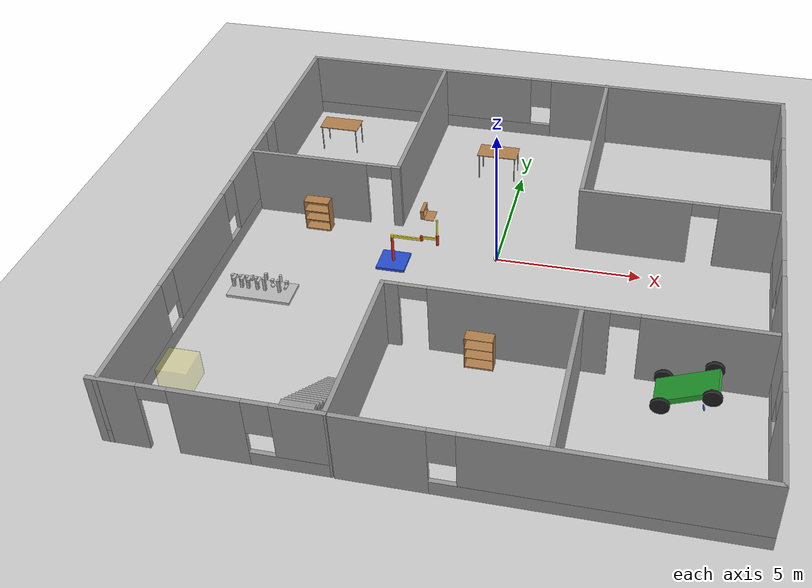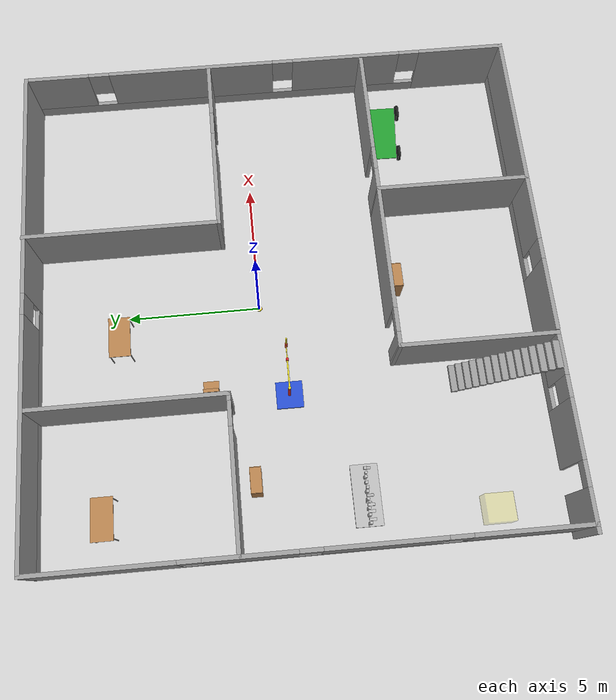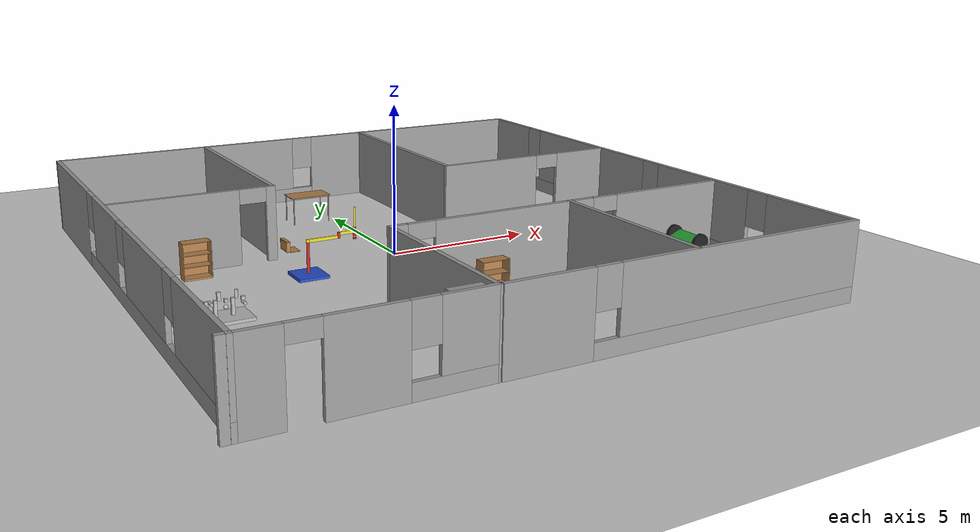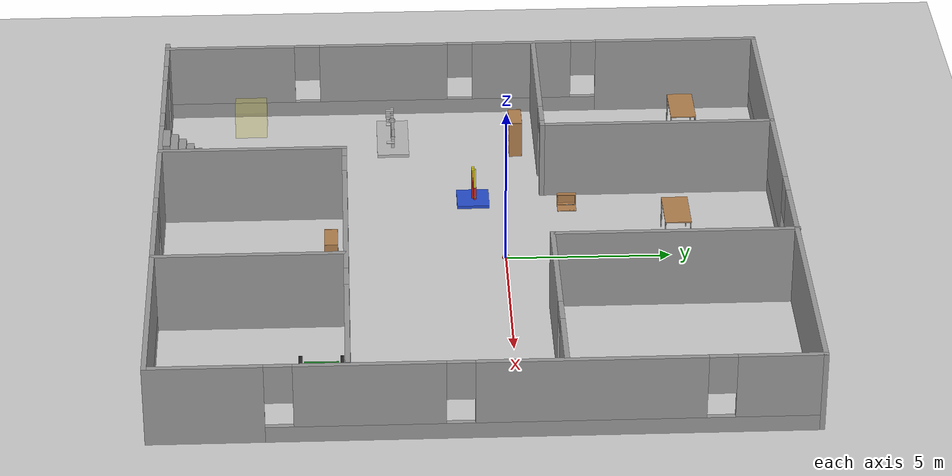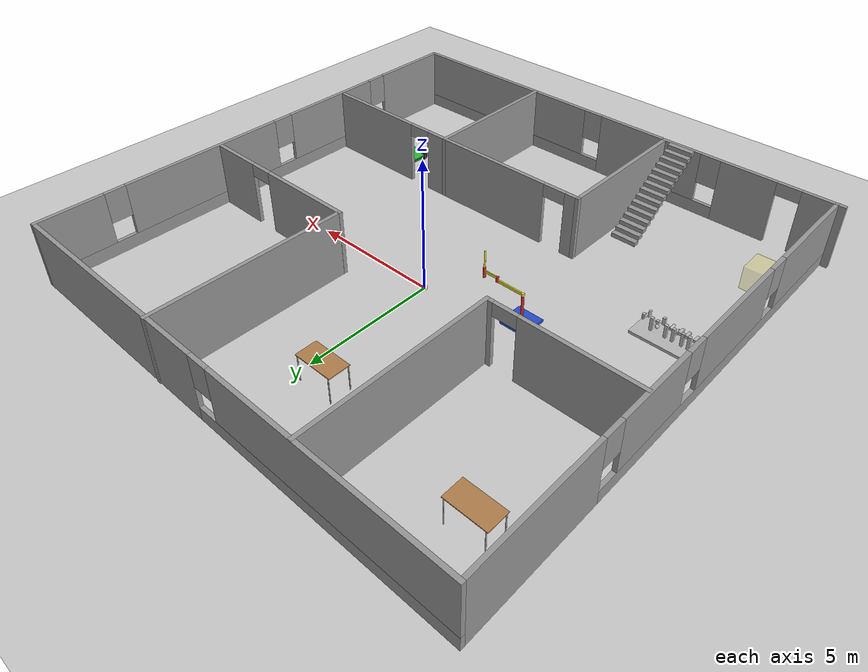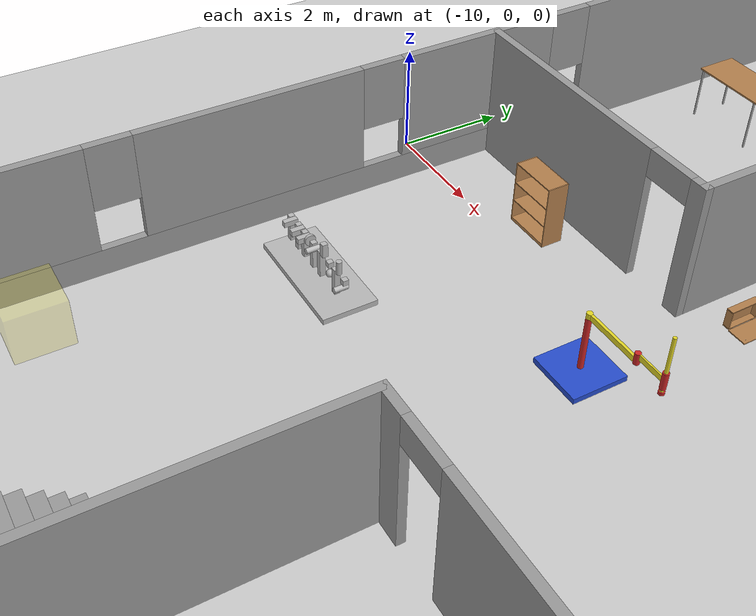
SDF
<sdf version="1.7">
 <world name="default">
  <light name="sun" type="directional">
   <pose>0 0 10 0 -0 0</pose>
   <diffuse>0.8 0.8 0.8 1</diffuse>
   <specular>0.2 0.2 0.2 1</specular>
   <attenuation>
    <range>1000</range>
    <constant>0.9</constant>
    <linear>0.01</linear>
    <quadratic>0.001</quadratic>
   </attenuation>
   <direction>-0.5 0.1 -0.9</direction>
   <spot><inner_angle>0</inner_angle><outer_angle>0</outer_angle><falloff>0</falloff></spot>
  </light>
  <model name="ground_plane">
   <static>1</static>
   <link name="link">
    <collision name="collision">
     <geometry><plane><normal>0 0 1</normal><size>100 100</size></plane></geometry>
     <surface><friction><ode><mu>100</mu><mu2>50</mu2></ode></friction></surface>
    </collision>
    <visual name="visual">
     <cast_shadows>0</cast_shadows>
     <geometry><plane><normal>0 0 1</normal><size>100 100</size></plane></geometry>
     <material>
      <script><uri>file://media/materials/scripts/gazebo.material</uri><name>Gazebo/Grey</name></script>
     </material>
    </visual>
   </link>
  </model>
  <gravity>0 0 -9.8</gravity>
  <magnetic_field>6e-06 2.3e-05 -4.2e-05</magnetic_field>
  <atmosphere type="adiabatic"/>
  <physics type="ode">
   <max_step_size>0.001</max_step_size>
   <real_time_factor>1</real_time_factor>
   <real_time_update_rate>1000</real_time_update_rate>
  </physics>
  <scene><ambient>0.4 0.4 0.4 1</ambient><background>0.7 0.7 0.7 1</background><shadows>1</shadows></scene>
  <spherical_coordinates>
   <surface_model>EARTH_WGS84</surface_model>
   <latitude_deg>0</latitude_deg>
   <longitude_deg>0</longitude_deg>
   <elevation>0</elevation>
   <heading_deg>0</heading_deg>
  </spherical_coordinates>
  <model name="mycar">
   <link name="base_footprint">
    <inertial>
     <pose>0.00127 0 0.093611 0 -0 0</pose>
     <mass>0.63</mass>
     <inertia>
      <ixx>0.00557395</ixx>
      <ixy>0</ixy>
      <ixz>-1.11111e-05</ixz>
      <iyy>0.00563694</iyy>
      <iyz>0</iyz>
      <izz>0.00261003</izz>
     </inertia>
    </inertial>
    <collision name="base_footprint_fixed_joint_lump__base_link_collision">
     <pose>0 0 0.055 0 -0 0</pose>
     <geometry><cylinder><length>0.08</length><radius>0.1</radius></cylinder></geometry>
    </collision>
    <collision name="base_footprint_fixed_joint_lump__camera_collision_1">
     <pose>0.08 0 0.1075 0 -0 0</pose>
     <geometry><box><size>0.01 0.025 0.025</size></box></geometry>
    </collision>
    <collision name="base_footprint_fixed_joint_lump__support_collision_2">
     <pose>0 0 0.17 0 -0 0</pose>
     <geometry><cylinder><length>0.15</length><radius>0.01</radius></cylinder></geometry>
    </collision>
    <collision name="base_footprint_fixed_joint_lump__laser_collision_3">
     <pose>0 0 0.27 0 -0 0</pose>
     <geometry><cylinder><length>0.05</length><radius>0.03</radius></cylinder></geometry>
    </collision>
    <visual name="base_footprint_visual"><geometry><sphere><radius>0.001</radius></sphere></geometry></visual>
    <visual name="base_footprint_fixed_joint_lump__base_link_visual_1">
     <pose>0 0 0.055 0 -0 0</pose>
     <geometry><cylinder><length>0.08</length><radius>0.1</radius></cylinder></geometry>
     <material>
      <script><name>Gazebo/Yellow</name><uri>file://media/materials/scripts/gazebo.material</uri></script>
     </material>
    </visual>
    <visual name="base_footprint_fixed_joint_lump__camera_visual_2">
     <pose>0.08 0 0.1075 0 -0 0</pose>
     <geometry><box><size>0.01 0.025 0.025</size></box></geometry>
     <material>
      <script><name>Gazebo/Blue</name><uri>file://media/materials/scripts/gazebo.material</uri></script>
     </material>
    </visual>
    <visual name="base_footprint_fixed_joint_lump__support_visual_3">
     <pose>0 0 0.17 0 -0 0</pose>
     <geometry><cylinder><length>0.15</length><radius>0.01</radius></cylinder></geometry>
     <material>
      <script><name>Gazebo/White</name><uri>file://media/materials/scripts/gazebo.material</uri></script>
     </material>
    </visual>
    <visual name="base_footprint_fixed_joint_lump__laser_visual_4">
     <pose>0 0 0.27 0 -0 0</pose>
     <geometry><cylinder><length>0.05</length><radius>0.03</radius></cylinder></geometry>
     <material>
      <script><name>Gazebo/Black</name><uri>file://media/materials/scripts/gazebo.material</uri></script>
     </material>
    </visual>
    <sensor name="camera_node" type="camera">
     <update_rate>30</update_rate>
     <camera name="head">
      <horizontal_fov>1.39626</horizontal_fov>
      <image><width>1280</width><height>720</height><format>R8G8B8</format></image>
      <clip><near>0.02</near><far>300</far></clip>
      <noise><type>gaussian</type><mean>0</mean><stddev>0.007</stddev></noise>
     </camera>
     <plugin name="gazebo_camera" filename="libgazebo_ros_camera.so">
      <alwaysOn>1</alwaysOn>
      <updateRate>0.0</updateRate>
      <cameraName>/camera</cameraName>
      <imageTopicName>image_raw</imageTopicName>
      <cameraInfoTopicName>camera_info</cameraInfoTopicName>
      <frameName>camera</frameName>
      <hackBaseline>0.07</hackBaseline>
      <distortionK1>0.0</distortionK1>
      <distortionK2>0.0</distortionK2>
      <distortionK3>0.0</distortionK3>
      <distortionT1>0.0</distortionT1>
      <distortionT2>0.0</distortionT2>
      <robotNamespace>/</robotNamespace>
     </plugin>
     <pose>0.08 0 0.1075 0 -0 0</pose>
    </sensor>
   </link>
   <joint name="back_wheel2base_link" type="revolute">
    <pose relative_to="base_footprint">-0.0925 0 0.0075 0 -0 0</pose>
    <parent>base_footprint</parent>
    <child>back_wheel</child>
    <axis>
     <xyz>1 1 1</xyz>
     <limit><lower>-1e+16</lower><upper>1e+16</upper></limit>
     <dynamics><spring_reference>0</spring_reference><spring_stiffness>0</spring_stiffness></dynamics>
    </axis>
   </joint>
   <link name="back_wheel">
    <pose relative_to="back_wheel2base_link">0 0 0 0 -0 0</pose>
    <inertial>
     <mass>0.03</mass>
     <inertia>
      <ixx>6.75e-07</ixx>
      <ixy>0</ixy>
      <ixz>0</ixz>
      <iyy>6.75e-07</iyy>
      <iyz>0</iyz>
      <izz>6.75e-07</izz>
     </inertia>
    </inertial>
    <collision name="back_wheel_collision">
     <geometry><sphere><radius>0.0075</radius></sphere></geometry>
    </collision>
    <visual name="back_wheel_visual">
     <geometry><sphere><radius>0.0075</radius></sphere></geometry>
     <material>
      <script><name>Gazebo/Red</name><uri>file://media/materials/scripts/gazebo.material</uri></script>
     </material>
    </visual>
   </link>
   <joint name="front_wheel2base_link" type="revolute">
    <pose relative_to="base_footprint">0.0925 0 0.0075 0 -0 0</pose>
    <parent>base_footprint</parent>
    <child>front_wheel</child>
    <axis>
     <xyz>1 1 1</xyz>
     <limit><lower>-1e+16</lower><upper>1e+16</upper></limit>
     <dynamics><spring_reference>0</spring_reference><spring_stiffness>0</spring_stiffness></dynamics>
    </axis>
   </joint>
   <link name="front_wheel">
    <pose relative_to="front_wheel2base_link">0 0 0 0 -0 0</pose>
    <inertial>
     <mass>0.03</mass>
     <inertia>
      <ixx>6.75e-07</ixx>
      <ixy>0</ixy>
      <ixz>0</ixz>
      <iyy>6.75e-07</iyy>
      <iyz>0</iyz>
      <izz>6.75e-07</izz>
     </inertia>
    </inertial>
    <collision name="front_wheel_collision">
     <geometry><sphere><radius>0.0075</radius></sphere></geometry>
    </collision>
    <visual name="front_wheel_visual">
     <geometry><sphere><radius>0.0075</radius></sphere></geometry>
     <material>
      <script><name>Gazebo/Red</name><uri>file://media/materials/scripts/gazebo.material</uri></script>
     </material>
    </visual>
   </link>
   <joint name="left_wheel2base_link" type="revolute">
    <pose relative_to="base_footprint">0 0.1 0.0325 0 -0 0</pose>
    <parent>base_footprint</parent>
    <child>left_wheel</child>
    <axis>
     <xyz>0 1 0</xyz>
     <limit><lower>-1e+16</lower><upper>1e+16</upper></limit>
     <dynamics><spring_reference>0</spring_reference><spring_stiffness>0</spring_stiffness></dynamics>
    </axis>
   </joint>
   <link name="left_wheel">
    <pose relative_to="left_wheel2base_link">0 0 0 0 -0 0</pose>
    <inertial>
     <mass>0.05</mass>
     <inertia>
      <ixx>1.41406e-05</ixx>
      <ixy>0</ixy>
      <ixz>0</ixz>
      <iyy>1.41406e-05</iyy>
      <iyz>0</iyz>
      <izz>2.64063e-05</izz>
     </inertia>
    </inertial>
    <collision name="left_wheel_collision">
     <pose>0 0 0 1.5708 -0 0</pose>
     <geometry><cylinder><length>0.015</length><radius>0.0325</radius></cylinder></geometry>
    </collision>
    <visual name="left_wheel_visual">
     <pose>0 0 0 1.5708 -0 0</pose>
     <geometry><cylinder><length>0.015</length><radius>0.0325</radius></cylinder></geometry>
     <material>
      <script><name>Gazebo/Red</name><uri>file://media/materials/scripts/gazebo.material</uri></script>
     </material>
    </visual>
   </link>
   <joint name="right_wheel2base_link" type="revolute">
    <pose relative_to="base_footprint">0 -0.1 0.0325 0 -0 0</pose>
    <parent>base_footprint</parent>
    <child>right_wheel</child>
    <axis>
     <xyz>0 1 0</xyz>
     <limit><lower>-1e+16</lower><upper>1e+16</upper></limit>
     <dynamics><spring_reference>0</spring_reference><spring_stiffness>0</spring_stiffness></dynamics>
    </axis>
   </joint>
   <link name="right_wheel">
    <pose relative_to="right_wheel2base_link">0 0 0 0 -0 0</pose>
    <inertial>
     <mass>0.05</mass>
     <inertia>
      <ixx>1.41406e-05</ixx>
      <ixy>0</ixy>
      <ixz>0</ixz>
      <iyy>1.41406e-05</iyy>
      <iyz>0</iyz>
      <izz>2.64063e-05</izz>
     </inertia>
    </inertial>
    <collision name="right_wheel_collision">
     <pose>0 0 0 1.5708 -0 0</pose>
     <geometry><cylinder><length>0.015</length><radius>0.0325</radius></cylinder></geometry>
    </collision>
    <visual name="right_wheel_visual">
     <pose>0 0 0 1.5708 -0 0</pose>
     <geometry><cylinder><length>0.015</length><radius>0.0325</radius></cylinder></geometry>
     <material>
      <script><name>Gazebo/Red</name><uri>file://media/materials/scripts/gazebo.material</uri></script>
     </material>
    </visual>
   </link>
   <static>0</static>
   <plugin name="differential_drive_controller" filename="libgazebo_ros_diff_drive.so">
    <rosDebugLevel>Debug</rosDebugLevel>
    <publishWheelTF>1</publishWheelTF>
    <robotNamespace>/</robotNamespace>
    <publishTf>1</publishTf>
    <publishWheelJointState>1</publishWheelJointState>
    <alwaysOn>1</alwaysOn>
    <updateRate>100.0</updateRate>
    <legacyMode>1</legacyMode>
    <leftJoint>left_wheel2base_link</leftJoint>
    <rightJoint>right_wheel2base_link</rightJoint>
    <wheelSeparation>0.2</wheelSeparation>
    <wheelDiameter>0.065</wheelDiameter>
    <broadcastTF>1</broadcastTF>
    <wheelTorque>30</wheelTorque>
    <wheelAcceleration>1.8</wheelAcceleration>
    <commandTopic>cmd_vel</commandTopic>
    <odometryFrame>odom</odometryFrame>
    <odometryTopic>odom</odometryTopic>
    <robotBaseFrame>base_footprint</robotBaseFrame>
   </plugin>
  </model>
  <model name="tony_house.world">
   <pose>0 -1 0 0 -0 0</pose>
   <link name="Stairs_0">
    <visual name="Stairs_0_Visual_0">
     <pose>-3.39052 -5.99335 0.083333 0 -0 0</pose>
     <geometry><box><size>1 0.233333 0.166667</size></box></geometry>
     <material>
      <script><uri>file://media/materials/scripts/gazebo.material</uri><name>Gazebo/Grey</name></script>
      <ambient>1 1 1 1</ambient>
     </material>
     <meta><layer>0</layer></meta>
    </visual>
    <collision name="Stairs_0_Collision_0">
     <geometry><box><size>1 0.233333 0.166667</size></box></geometry>
     <pose>-3.39052 -5.99335 0.083333 0 -0 0</pose>
    </collision>
    <visual name="Stairs_0_Visual_1">
     <pose>-3.39052 -6.22668 0.25 0 -0 0</pose>
     <geometry><box><size>1 0.233333 0.166667</size></box></geometry>
     <material>
      <script><uri>file://media/materials/scripts/gazebo.material</uri><name>Gazebo/Grey</name></script>
      <ambient>1 1 1 1</ambient>
     </material>
     <meta><layer>0</layer></meta>
    </visual>
    <collision name="Stairs_0_Collision_1">
     <geometry><box><size>1 0.233333 0.166667</size></box></geometry>
     <pose>-3.39052 -6.22668 0.25 0 -0 0</pose>
    </collision>
    <visual name="Stairs_0_Visual_2">
     <pose>-3.39052 -6.46001 0.416667 0 -0 0</pose>
     <geometry><box><size>1 0.233333 0.166667</size></box></geometry>
     <material>
      <script><uri>file://media/materials/scripts/gazebo.material</uri><name>Gazebo/Grey</name></script>
      <ambient>1 1 1 1</ambient>
     </material>
     <meta><layer>0</layer></meta>
    </visual>
    <collision name="Stairs_0_Collision_2">
     <geometry><box><size>1 0.233333 0.166667</size></box></geometry>
     <pose>-3.39052 -6.46001 0.416667 0 -0 0</pose>
    </collision>
    <visual name="Stairs_0_Visual_3">
     <pose>-3.39052 -6.69335 0.583333 0 -0 0</pose>
     <geometry><box><size>1 0.233333 0.166667</size></box></geometry>
     <material>
      <script><uri>file://media/materials/scripts/gazebo.material</uri><name>Gazebo/Grey</name></script>
      <ambient>1 1 1 1</ambient>
     </material>
     <meta><layer>0</layer></meta>
    </visual>
    <collision name="Stairs_0_Collision_3">
     <geometry><box><size>1 0.233333 0.166667</size></box></geometry>
     <pose>-3.39052 -6.69335 0.583333 0 -0 0</pose>
    </collision>
    <visual name="Stairs_0_Visual_4">
     <pose>-3.39052 -6.92668 0.75 0 -0 0</pose>
     <geometry><box><size>1 0.233333 0.166667</size></box></geometry>
     <material>
      <script><uri>file://media/materials/scripts/gazebo.material</uri><name>Gazebo/Grey</name></script>
      <ambient>1 1 1 1</ambient>
     </material>
     <meta><layer>0</layer></meta>
    </visual>
    <collision name="Stairs_0_Collision_4">
     <geometry><box><size>1 0.233333 0.166667</size></box></geometry>
     <pose>-3.39052 -6.92668 0.75 0 -0 0</pose>
    </collision>
    <visual name="Stairs_0_Visual_5">
     <pose>-3.39052 -7.16001 0.916667 0 -0 0</pose>
     <geometry><box><size>1 0.233333 0.166667</size></box></geometry>
     <material>
      <script><uri>file://media/materials/scripts/gazebo.material</uri><name>Gazebo/Grey</name></script>
      <ambient>1 1 1 1</ambient>
     </material>
     <meta><layer>0</layer></meta>
    </visual>
    <collision name="Stairs_0_Collision_5">
     <geometry><box><size>1 0.233333 0.166667</size></box></geometry>
     <pose>-3.39052 -7.16001 0.916667 0 -0 0</pose>
    </collision>
    <visual name="Stairs_0_Visual_6">
     <pose>-3.39052 -7.39335 1.08333 0 -0 0</pose>
     <geometry><box><size>1 0.233333 0.166667</size></box></geometry>
     <material>
      <script><uri>file://media/materials/scripts/gazebo.material</uri><name>Gazebo/Grey</name></script>
      <ambient>1 1 1 1</ambient>
     </material>
     <meta><layer>0</layer></meta>
    </visual>
    <collision name="Stairs_0_Collision_6">
     <geometry><box><size>1 0.233333 0.166667</size></box></geometry>
     <pose>-3.39052 -7.39335 1.08333 0 -0 0</pose>
    </collision>
    <visual name="Stairs_0_Visual_7">
     <pose>-3.39052 -7.62668 1.25 0 -0 0</pose>
     <geometry><box><size>1 0.233333 0.166667</size></box></geometry>
     <material>
      <script><uri>file://media/materials/scripts/gazebo.material</uri><name>Gazebo/Grey</name></script>
      <ambient>1 1 1 1</ambient>
     </material>
     <meta><layer>0</layer></meta>
    </visual>
    <collision name="Stairs_0_Collision_7">
     <geometry><box><size>1 0.233333 0.166667</size></box></geometry>
     <pose>-3.39052 -7.62668 1.25 0 -0 0</pose>
    </collision>
    <visual name="Stairs_0_Visual_8">
     <pose>-3.39052 -7.86001 1.41667 0 -0 0</pose>
     <geometry><box><size>1 0.233333 0.166667</size></box></geometry>
     <material>
      <script><uri>file://media/materials/scripts/gazebo.material</uri><name>Gazebo/Grey</name></script>
      <ambient>1 1 1 1</ambient>
     </material>
     <meta><layer>0</layer></meta>
    </visual>
    <collision name="Stairs_0_Collision_8">
     <geometry><box><size>1 0.233333 0.166667</size></box></geometry>
     <pose>-3.39052 -7.86001 1.41667 0 -0 0</pose>
    </collision>
    <visual name="Stairs_0_Visual_9">
     <pose>-3.39052 -8.09335 1.58333 0 -0 0</pose>
     <geometry><box><size>1 0.233333 0.166667</size></box></geometry>
     <material>
      <script><uri>file://media/materials/scripts/gazebo.material</uri><name>Gazebo/Grey</name></script>
      <ambient>1 1 1 1</ambient>
     </material>
     <meta><layer>0</layer></meta>
    </visual>
    <collision name="Stairs_0_Collision_9">
     <geometry><box><size>1 0.233333 0.166667</size></box></geometry>
     <pose>-3.39052 -8.09335 1.58333 0 -0 0</pose>
    </collision>
    <visual name="Stairs_0_Visual_10">
     <pose>-3.39052 -8.32668 1.75 0 -0 0</pose>
     <geometry><box><size>1 0.233333 0.166667</size></box></geometry>
     <material>
      <script><uri>file://media/materials/scripts/gazebo.material</uri><name>Gazebo/Grey</name></script>
      <ambient>1 1 1 1</ambient>
     </material>
     <meta><layer>0</layer></meta>
    </visual>
    <collision name="Stairs_0_Collision_10">
     <geometry><box><size>1 0.233333 0.166667</size></box></geometry>
     <pose>-3.39052 -8.32668 1.75 0 -0 0</pose>
    </collision>
    <visual name="Stairs_0_Visual_11">
     <pose>-3.39052 -8.56001 1.91667 0 -0 0</pose>
     <geometry><box><size>1 0.233333 0.166667</size></box></geometry>
     <material>
      <script><uri>file://media/materials/scripts/gazebo.material</uri><name>Gazebo/Grey</name></script>
      <ambient>1 1 1 1</ambient>
     </material>
     <meta><layer>0</layer></meta>
    </visual>
    <collision name="Stairs_0_Collision_11">
     <geometry><box><size>1 0.233333 0.166667</size></box></geometry>
     <pose>-3.39052 -8.56001 1.91667 0 -0 0</pose>
    </collision>
    <visual name="Stairs_0_Visual_12">
     <pose>-3.39052 -8.79335 2.08333 0 -0 0</pose>
     <geometry><box><size>1 0.233333 0.166667</size></box></geometry>
     <material>
      <script><uri>file://media/materials/scripts/gazebo.material</uri><name>Gazebo/Grey</name></script>
      <ambient>1 1 1 1</ambient>
     </material>
     <meta><layer>0</layer></meta>
    </visual>
    <collision name="Stairs_0_Collision_12">
     <geometry><box><size>1 0.233333 0.166667</size></box></geometry>
     <pose>-3.39052 -8.79335 2.08333 0 -0 0</pose>
    </collision>
    <visual name="Stairs_0_Visual_13">
     <pose>-3.39052 -9.02668 2.25 0 -0 0</pose>
     <geometry><box><size>1 0.233333 0.166667</size></box></geometry>
     <material>
      <script><uri>file://media/materials/scripts/gazebo.material</uri><name>Gazebo/Grey</name></script>
      <ambient>1 1 1 1</ambient>
     </material>
     <meta><layer>0</layer></meta>
    </visual>
    <collision name="Stairs_0_Collision_13">
     <geometry><box><size>1 0.233333 0.166667</size></box></geometry>
     <pose>-3.39052 -9.02668 2.25 0 -0 0</pose>
    </collision>
    <visual name="Stairs_0_Visual_14">
     <pose>-3.39052 -9.26001 2.41667 0 -0 0</pose>
     <geometry><box><size>1 0.233333 0.166667</size></box></geometry>
     <material>
      <script><uri>file://media/materials/scripts/gazebo.material</uri><name>Gazebo/Grey</name></script>
      <ambient>1 1 1 1</ambient>
     </material>
     <meta><layer>0</layer></meta>
    </visual>
    <collision name="Stairs_0_Collision_14">
     <geometry><box><size>1 0.233333 0.166667</size></box></geometry>
     <pose>-3.39052 -9.26001 2.41667 0 -0 0</pose>
    </collision>
   </link>
   <link name="Wall_1">
    <pose>-6.01156 -9.43056 0 0 -0 0.001171</pose>
    <visual name="Wall_1_Visual_0">
     <pose>-2.72986 0 1.25 0 -0 0</pose>
     <geometry><box><size>1.51416 0.15 2.5</size></box></geometry>
     <material>
      <script><uri>file://media/materials/scripts/gazebo.material</uri><name>Gazebo/Grey</name></script>
      <ambient>1 1 1 1</ambient>
     </material>
     <meta><layer>0</layer></meta>
    </visual>
    <collision name="Wall_1_Collision_0">
     <geometry><box><size>1.51416 0.15 2.5</size></box></geometry>
     <pose>-2.72986 0 1.25 0 -0 0</pose>
    </collision>
    <visual name="Wall_1_Visual_1">
     <pose>-0.004916 0 1.25 0 -0 0</pose>
     <geometry><box><size>2.13573 0.15 2.5</size></box></geometry>
     <material>
      <script><uri>file://media/materials/scripts/gazebo.material</uri><name>Gazebo/Grey</name></script>
      <ambient>1 1 1 1</ambient>
     </material>
     <meta><layer>0</layer></meta>
    </visual>
    <collision name="Wall_1_Collision_1">
     <geometry><box><size>2.13573 0.15 2.5</size></box></geometry>
     <pose>-0.004916 0 1.25 0 -0 0</pose>
    </collision>
    <visual name="Wall_1_Visual_2">
     <pose>2.27494 0 0.25 0 -0 0</pose>
     <geometry><box><size>2.42399 0.15 0.5</size></box></geometry>
     <material>
      <script><uri>file://media/materials/scripts/gazebo.material</uri><name>Gazebo/Grey</name></script>
      <ambient>1 1 1 1</ambient>
     </material>
     <meta><layer>0</layer></meta>
    </visual>
    <collision name="Wall_1_Collision_2">
     <geometry><box><size>2.42399 0.15 0.5</size></box></geometry>
     <pose>2.27494 0 0.25 0 -0 0</pose>
    </collision>
    <visual name="Wall_1_Visual_3">
     <pose>2.67494 0 1.5 0 -0 0</pose>
     <geometry><box><size>1.62399 0.15 2</size></box></geometry>
     <material>
      <script><uri>file://media/materials/scripts/gazebo.material</uri><name>Gazebo/Grey</name></script>
      <ambient>1 1 1 1</ambient>
     </material>
     <meta><layer>0</layer></meta>
    </visual>
    <collision name="Wall_1_Collision_3">
     <geometry><box><size>1.62399 0.15 2</size></box></geometry>
     <pose>2.67494 0 1.5 0 -0 0</pose>
    </collision>
    <visual name="Wall_1_Visual_4">
     <pose>1.46295 0 1.9 0 -0 0</pose>
     <geometry><box><size>0.8 0.15 1.2</size></box></geometry>
     <material>
      <script><uri>file://media/materials/scripts/gazebo.material</uri><name>Gazebo/Grey</name></script>
      <ambient>1 1 1 1</ambient>
     </material>
     <meta><layer>0</layer></meta>
    </visual>
    <collision name="Wall_1_Collision_4">
     <geometry><box><size>0.8 0.15 1.2</size></box></geometry>
     <pose>1.46295 0 1.9 0 -0 0</pose>
    </collision>
    <visual name="Wall_1_Visual_5">
     <pose>-1.52278 0 2.25 0 -0 0</pose>
     <geometry><box><size>0.9 0.15 0.5</size></box></geometry>
     <material>
      <script><uri>file://media/materials/scripts/gazebo.material</uri><name>Gazebo/Grey</name></script>
      <ambient>1 1 1 1</ambient>
     </material>
     <meta><layer>0</layer></meta>
    </visual>
    <collision name="Wall_1_Collision_5">
     <geometry><box><size>0.9 0.15 0.5</size></box></geometry>
     <pose>-1.52278 0 2.25 0 -0 0</pose>
    </collision>
   </link>
   <link name="Wall_10">
    <pose>3.32538 -3.82656 0 0 -0 0</pose>
    <visual name="Wall_10_Visual_0">
     <pose>-5.70576 0 1.25 0 -0 0</pose>
     <geometry><box><size>0.588485 0.15 2.5</size></box></geometry>
     <material>
      <script><uri>file://media/materials/scripts/gazebo.material</uri><name>Gazebo/Grey</name></script>
      <ambient>1 1 1 1</ambient>
     </material>
     <meta><layer>0</layer></meta>
    </visual>
    <collision name="Wall_10_Collision_0">
     <geometry><box><size>0.588485 0.15 2.5</size></box></geometry>
     <pose>-5.70576 0 1.25 0 -0 0</pose>
    </collision>
    <visual name="Wall_10_Visual_1">
     <pose>-1.72323 0 1.25 0 -0 0</pose>
     <geometry><box><size>5.57657 0.15 2.5</size></box></geometry>
     <material>
      <script><uri>file://media/materials/scripts/gazebo.material</uri><name>Gazebo/Grey</name></script>
      <ambient>1 1 1 1</ambient>
     </material>
     <meta><layer>0</layer></meta>
    </visual>
    <collision name="Wall_10_Collision_1">
     <geometry><box><size>5.57657 0.15 2.5</size></box></geometry>
     <pose>-1.72323 0 1.25 0 -0 0</pose>
    </collision>
    <visual name="Wall_10_Visual_2">
     <pose>3.98253 0 1.25 0 -0 0</pose>
     <geometry><box><size>4.03494 0.15 2.5</size></box></geometry>
     <material>
      <script><uri>file://media/materials/scripts/gazebo.material</uri><name>Gazebo/Grey</name></script>
      <ambient>1 1 1 1</ambient>
     </material>
     <meta><layer>0</layer></meta>
    </visual>
    <collision name="Wall_10_Collision_2">
     <geometry><box><size>4.03494 0.15 2.5</size></box></geometry>
     <pose>3.98253 0 1.25 0 -0 0</pose>
    </collision>
    <visual name="Wall_10_Visual_3">
     <pose>-4.96152 0 2.25 0 -0 0</pose>
     <geometry><box><size>0.9 0.15 0.5</size></box></geometry>
     <material>
      <script><uri>file://media/materials/scripts/gazebo.material</uri><name>Gazebo/Grey</name></script>
      <ambient>1 1 1 1</ambient>
     </material>
     <meta><layer>0</layer></meta>
    </visual>
    <collision name="Wall_10_Collision_3">
     <geometry><box><size>0.9 0.15 0.5</size></box></geometry>
     <pose>-4.96152 0 2.25 0 -0 0</pose>
    </collision>
    <visual name="Wall_10_Visual_4">
     <pose>1.51506 0 2.25 0 -0 0</pose>
     <geometry><box><size>0.9 0.15 0.5</size></box></geometry>
     <material>
      <script><uri>file://media/materials/scripts/gazebo.material</uri><name>Gazebo/Grey</name></script>
      <ambient>1 1 1 1</ambient>
     </material>
     <meta><layer>0</layer></meta>
    </visual>
    <collision name="Wall_10_Collision_4">
     <geometry><box><size>0.9 0.15 0.5</size></box></geometry>
     <pose>1.51506 0 2.25 0 -0 0</pose>
    </collision>
   </link>
   <link name="Wall_12">
    <collision name="Wall_12_Collision">
     <geometry><box><size>5.75 0.15 2.5</size></box></geometry>
     <pose>0 0 1.25 0 -0 0</pose>
    </collision>
    <visual name="Wall_12_Visual">
     <pose>0 0 1.25 0 -0 0</pose>
     <geometry><box><size>5.75 0.15 2.5</size></box></geometry>
     <material>
      <script><uri>file://media/materials/scripts/gazebo.material</uri><name>Gazebo/Grey</name></script>
      <ambient>1 1 1 1</ambient>
     </material>
     <meta><layer>0</layer></meta>
    </visual>
    <pose>3.54453 -6.62656 0 0 -0 -1.5708</pose>
   </link>
   <link name="Wall_14">
    <pose>5.98556 2.23237 0 0 -0 0</pose>
    <visual name="Wall_14_Visual_0">
     <pose>-1.46444 0 1.25 0 -0 0</pose>
     <geometry><box><size>3.82112 0.15 2.5</size></box></geometry>
     <material>
      <script><uri>file://media/materials/scripts/gazebo.material</uri><name>Gazebo/Grey</name></script>
      <ambient>1 1 1 1</ambient>
     </material>
     <meta><layer>0</layer></meta>
    </visual>
    <collision name="Wall_14_Collision_0">
     <geometry><box><size>3.82112 0.15 2.5</size></box></geometry>
     <pose>-1.46444 0 1.25 0 -0 0</pose>
    </collision>
    <visual name="Wall_14_Visual_1">
     <pose>2.36056 0 1.25 0 -0 0</pose>
     <geometry><box><size>2.02888 0.15 2.5</size></box></geometry>
     <material>
      <script><uri>file://media/materials/scripts/gazebo.material</uri><name>Gazebo/Grey</name></script>
      <ambient>1 1 1 1</ambient>
     </material>
     <meta><layer>0</layer></meta>
    </visual>
    <collision name="Wall_14_Collision_1">
     <geometry><box><size>2.02888 0.15 2.5</size></box></geometry>
     <pose>2.36056 0 1.25 0 -0 0</pose>
    </collision>
    <visual name="Wall_14_Visual_2">
     <pose>0.896121 0 2.25 0 -0 0</pose>
     <geometry><box><size>0.9 0.15 0.5</size></box></geometry>
     <material>
      <script><uri>file://media/materials/scripts/gazebo.material</uri><name>Gazebo/Grey</name></script>
      <ambient>1 1 1 1</ambient>
     </material>
     <meta><layer>0</layer></meta>
    </visual>
    <collision name="Wall_14_Collision_2">
     <geometry><box><size>0.9 0.15 0.5</size></box></geometry>
     <pose>0.896121 0 2.25 0 -0 0</pose>
    </collision>
   </link>
   <link name="Wall_18">
    <collision name="Wall_18_Collision">
     <geometry><box><size>7.25 0.15 2.5</size></box></geometry>
     <pose>0 0 1.25 0 -0 0</pose>
    </collision>
    <visual name="Wall_18_Visual">
     <pose>0 0 1.25 0 -0 0</pose>
     <geometry><box><size>7.25 0.15 2.5</size></box></geometry>
     <material>
      <script><uri>file://media/materials/scripts/gazebo.material</uri><name>Gazebo/Grey</name></script>
      <ambient>1 1 1 1</ambient>
     </material>
     <meta><layer>0</layer></meta>
    </visual>
    <pose>-3.77724 5.84349 0 0 -0 -1.5708</pose>
   </link>
   <link name="Wall_20">
    <collision name="Wall_20_Collision">
     <geometry><box><size>7.25 0.15 2.5</size></box></geometry>
     <pose>0 0 1.25 0 -0 0</pose>
    </collision>
    <visual name="Wall_20_Visual">
     <pose>0 0 1.25 0 -0 0</pose>
     <geometry><box><size>7.25 0.15 2.5</size></box></geometry>
     <material>
      <script><uri>file://media/materials/scripts/gazebo.material</uri><name>Gazebo/Grey</name></script>
      <ambient>1 1 1 1</ambient>
     </material>
     <meta><layer>0</layer></meta>
    </visual>
    <pose>2.68958 5.89002 0 0 -0 -1.5708</pose>
   </link>
   <link name="Wall_22">
    <pose>-6.45224 2.29349 0 0 -0 3.14159</pose>
    <visual name="Wall_22_Visual_0">
     <pose>-2.58857 0 1.25 0 -0 0</pose>
     <geometry><box><size>0.322859 0.15 2.5</size></box></geometry>
     <material>
      <script><uri>file://media/materials/scripts/gazebo.material</uri><name>Gazebo/Grey</name></script>
      <ambient>1 1 1 1</ambient>
     </material>
     <meta><layer>0</layer></meta>
    </visual>
    <collision name="Wall_22_Collision_0">
     <geometry><box><size>0.322859 0.15 2.5</size></box></geometry>
     <pose>-2.58857 0 1.25 0 -0 0</pose>
    </collision>
    <visual name="Wall_22_Visual_1">
     <pose>0.611429 0 1.25 0 -0 0</pose>
     <geometry><box><size>4.27714 0.15 2.5</size></box></geometry>
     <material>
      <script><uri>file://media/materials/scripts/gazebo.material</uri><name>Gazebo/Grey</name></script>
      <ambient>1 1 1 1</ambient>
     </material>
     <meta><layer>0</layer></meta>
    </visual>
    <collision name="Wall_22_Collision_1">
     <geometry><box><size>4.27714 0.15 2.5</size></box></geometry>
     <pose>0.611429 0 1.25 0 -0 0</pose>
    </collision>
    <visual name="Wall_22_Visual_2">
     <pose>-1.97714 0 2.25 0 -0 0</pose>
     <geometry><box><size>0.9 0.15 0.5</size></box></geometry>
     <material>
      <script><uri>file://media/materials/scripts/gazebo.material</uri><name>Gazebo/Grey</name></script>
      <ambient>1 1 1 1</ambient>
     </material>
     <meta><layer>0</layer></meta>
    </visual>
    <collision name="Wall_22_Collision_2">
     <geometry><box><size>0.9 0.15 0.5</size></box></geometry>
     <pose>-1.97714 0 2.25 0 -0 0</pose>
    </collision>
   </link>
   <link name="Wall_24">
    <collision name="Wall_24_Collision">
     <geometry><box><size>5.75 0.15 2.5</size></box></geometry>
     <pose>0 0 1.25 0 -0 0</pose>
    </collision>
    <visual name="Wall_24_Visual">
     <pose>0 0 1.25 0 -0 0</pose>
     <geometry><box><size>5.75 0.15 2.5</size></box></geometry>
     <material>
      <script><uri>file://media/materials/scripts/gazebo.material</uri><name>Gazebo/Grey</name></script>
      <ambient>1 1 1 1</ambient>
     </material>
     <meta><layer>0</layer></meta>
    </visual>
    <pose>-2.59962 -6.62656 0 0 -0 -1.5708</pose>
   </link>
   <link name="Wall_3">
    <pose>3.49858 -9.44002 0 0 -0 0</pose>
    <visual name="Wall_3_Visual_0">
     <pose>-4.64469 0 1.25 0 -0 0</pose>
     <geometry><box><size>2.71062 0.15 2.5</size></box></geometry>
     <material>
      <script><uri>file://media/materials/scripts/gazebo.material</uri><name>Gazebo/Grey</name></script>
      <ambient>1 1 1 1</ambient>
     </material>
     <meta><layer>0</layer></meta>
    </visual>
    <collision name="Wall_3_Collision_0">
     <geometry><box><size>2.71062 0.15 2.5</size></box></geometry>
     <pose>-4.64469 0 1.25 0 -0 0</pose>
    </collision>
    <visual name="Wall_3_Visual_1">
     <pose>1.35531 0 0.25 0 -0 0</pose>
     <geometry><box><size>9.28938 0.15 0.5</size></box></geometry>
     <material>
      <script><uri>file://media/materials/scripts/gazebo.material</uri><name>Gazebo/Grey</name></script>
      <ambient>1 1 1 1</ambient>
     </material>
     <meta><layer>0</layer></meta>
    </visual>
    <collision name="Wall_3_Collision_1">
     <geometry><box><size>9.28938 0.15 0.5</size></box></geometry>
     <pose>1.35531 0 0.25 0 -0 0</pose>
    </collision>
    <visual name="Wall_3_Visual_2">
     <pose>1.75531 0 1.5 0 -0 0</pose>
     <geometry><box><size>8.48938 0.15 2</size></box></geometry>
     <material>
      <script><uri>file://media/materials/scripts/gazebo.material</uri><name>Gazebo/Grey</name></script>
      <ambient>1 1 1 1</ambient>
     </material>
     <meta><layer>0</layer></meta>
    </visual>
    <collision name="Wall_3_Collision_2">
     <geometry><box><size>8.48938 0.15 2</size></box></geometry>
     <pose>1.75531 0 1.5 0 -0 0</pose>
    </collision>
    <visual name="Wall_3_Visual_3">
     <pose>-2.88938 0 1.9 0 -0 0</pose>
     <geometry><box><size>0.8 0.15 1.2</size></box></geometry>
     <material>
      <script><uri>file://media/materials/scripts/gazebo.material</uri><name>Gazebo/Grey</name></script>
      <ambient>1 1 1 1</ambient>
     </material>
     <meta><layer>0</layer></meta>
    </visual>
    <collision name="Wall_3_Collision_3">
     <geometry><box><size>0.8 0.15 1.2</size></box></geometry>
     <pose>-2.88938 0 1.9 0 -0 0</pose>
    </collision>
   </link>
   <link name="Wall_4">
    <pose>9.42358 -0.015016 0 0 -0 1.5708</pose>
    <visual name="Wall_4_Visual_0">
     <pose>-7.8218 0 1.25 0 -0 0</pose>
     <geometry><box><size>3.3564 0.15 2.5</size></box></geometry>
     <material>
      <script><uri>file://media/materials/scripts/gazebo.material</uri><name>Gazebo/Grey</name></script>
      <ambient>1 1 1 1</ambient>
     </material>
     <meta><layer>0</layer></meta>
    </visual>
    <collision name="Wall_4_Collision_0">
     <geometry><box><size>3.3564 0.15 2.5</size></box></geometry>
     <pose>-7.8218 0 1.25 0 -0 0</pose>
    </collision>
    <visual name="Wall_4_Visual_1">
     <pose>1.6782 0 0.25 0 -0 0</pose>
     <geometry><box><size>15.6436 0.15 0.5</size></box></geometry>
     <material>
      <script><uri>file://media/materials/scripts/gazebo.material</uri><name>Gazebo/Grey</name></script>
      <ambient>1 1 1 1</ambient>
     </material>
     <meta><layer>0</layer></meta>
    </visual>
    <collision name="Wall_4_Collision_1">
     <geometry><box><size>15.6436 0.15 0.5</size></box></geometry>
     <pose>1.6782 0 0.25 0 -0 0</pose>
    </collision>
    <visual name="Wall_4_Visual_2">
     <pose>-3.21561 0 1.5 0 -0 0</pose>
     <geometry><box><size>4.25599 0.15 2</size></box></geometry>
     <material>
      <script><uri>file://media/materials/scripts/gazebo.material</uri><name>Gazebo/Grey</name></script>
      <ambient>1 1 1 1</ambient>
     </material>
     <meta><layer>0</layer></meta>
    </visual>
    <collision name="Wall_4_Collision_2">
     <geometry><box><size>4.25599 0.15 2</size></box></geometry>
     <pose>-3.21561 0 1.5 0 -0 0</pose>
    </collision>
    <visual name="Wall_4_Visual_3">
     <pose>2.94431 0 1.5 0 -0 0</pose>
     <geometry><box><size>6.46384 0.15 2</size></box></geometry>
     <material>
      <script><uri>file://media/materials/scripts/gazebo.material</uri><name>Gazebo/Grey</name></script>
      <ambient>1 1 1 1</ambient>
     </material>
     <meta><layer>0</layer></meta>
    </visual>
    <collision name="Wall_4_Collision_3">
     <geometry><box><size>6.46384 0.15 2</size></box></geometry>
     <pose>2.94431 0 1.5 0 -0 0</pose>
    </collision>
    <visual name="Wall_4_Visual_4">
     <pose>8.23811 0 1.5 0 -0 0</pose>
     <geometry><box><size>2.52377 0.15 2</size></box></geometry>
     <material>
      <script><uri>file://media/materials/scripts/gazebo.material</uri><name>Gazebo/Grey</name></script>
      <ambient>1 1 1 1</ambient>
     </material>
     <meta><layer>0</layer></meta>
    </visual>
    <collision name="Wall_4_Collision_4">
     <geometry><box><size>2.52377 0.15 2</size></box></geometry>
     <pose>8.23811 0 1.5 0 -0 0</pose>
    </collision>
    <visual name="Wall_4_Visual_5">
     <pose>-5.7436 0 1.9 0 -0 0</pose>
     <geometry><box><size>0.8 0.15 1.2</size></box></geometry>
     <material>
      <script><uri>file://media/materials/scripts/gazebo.material</uri><name>Gazebo/Grey</name></script>
      <ambient>1 1 1 1</ambient>
     </material>
     <meta><layer>0</layer></meta>
    </visual>
    <collision name="Wall_4_Collision_5">
     <geometry><box><size>0.8 0.15 1.2</size></box></geometry>
     <pose>-5.7436 0 1.9 0 -0 0</pose>
    </collision>
    <visual name="Wall_4_Visual_6">
     <pose>-0.687612 0 1.9 0 -0 0</pose>
     <geometry><box><size>0.8 0.15 1.2</size></box></geometry>
     <material>
      <script><uri>file://media/materials/scripts/gazebo.material</uri><name>Gazebo/Grey</name></script>
      <ambient>1 1 1 1</ambient>
     </material>
     <meta><layer>0</layer></meta>
    </visual>
    <collision name="Wall_4_Collision_6">
     <geometry><box><size>0.8 0.15 1.2</size></box></geometry>
     <pose>-0.687612 0 1.9 0 -0 0</pose>
    </collision>
    <visual name="Wall_4_Visual_7">
     <pose>6.57623 0 1.9 0 -0 0</pose>
     <geometry><box><size>0.8 0.15 1.2</size></box></geometry>
     <material>
      <script><uri>file://media/materials/scripts/gazebo.material</uri><name>Gazebo/Grey</name></script>
      <ambient>1 1 1 1</ambient>
     </material>
     <meta><layer>0</layer></meta>
    </visual>
    <collision name="Wall_4_Collision_7">
     <geometry><box><size>0.8 0.15 1.2</size></box></geometry>
     <pose>6.57623 0 1.9 0 -0 0</pose>
    </collision>
   </link>
   <link name="Wall_5">
    <pose>0.123583 9.40998 0 0 -0 3.14159</pose>
    <visual name="Wall_5_Visual_0">
     <pose>-4.87823 0 1.25 0 -0 0</pose>
     <geometry><box><size>8.99354 0.15 2.5</size></box></geometry>
     <material>
      <script><uri>file://media/materials/scripts/gazebo.material</uri><name>Gazebo/Grey</name></script>
      <ambient>1 1 1 1</ambient>
     </material>
     <meta><layer>0</layer></meta>
    </visual>
    <collision name="Wall_5_Collision_0">
     <geometry><box><size>8.99354 0.15 2.5</size></box></geometry>
     <pose>-4.87823 0 1.25 0 -0 0</pose>
    </collision>
    <visual name="Wall_5_Visual_1">
     <pose>4.49677 0 0.25 0 -0 0</pose>
     <geometry><box><size>9.75646 0.15 0.5</size></box></geometry>
     <material>
      <script><uri>file://media/materials/scripts/gazebo.material</uri><name>Gazebo/Grey</name></script>
      <ambient>1 1 1 1</ambient>
     </material>
     <meta><layer>0</layer></meta>
    </visual>
    <collision name="Wall_5_Collision_1">
     <geometry><box><size>9.75646 0.15 0.5</size></box></geometry>
     <pose>4.49677 0 0.25 0 -0 0</pose>
    </collision>
    <visual name="Wall_5_Visual_2">
     <pose>4.89677 0 1.5 0 -0 0</pose>
     <geometry><box><size>8.95646 0.15 2</size></box></geometry>
     <material>
      <script><uri>file://media/materials/scripts/gazebo.material</uri><name>Gazebo/Grey</name></script>
      <ambient>1 1 1 1</ambient>
     </material>
     <meta><layer>0</layer></meta>
    </visual>
    <collision name="Wall_5_Collision_2">
     <geometry><box><size>8.95646 0.15 2</size></box></geometry>
     <pose>4.89677 0 1.5 0 -0 0</pose>
    </collision>
    <visual name="Wall_5_Visual_3">
     <pose>0.018538 0 1.9 0 -0 0</pose>
     <geometry><box><size>0.8 0.15 1.2</size></box></geometry>
     <material>
      <script><uri>file://media/materials/scripts/gazebo.material</uri><name>Gazebo/Grey</name></script>
      <ambient>1 1 1 1</ambient>
     </material>
     <meta><layer>0</layer></meta>
    </visual>
    <collision name="Wall_5_Collision_3">
     <geometry><box><size>0.8 0.15 1.2</size></box></geometry>
     <pose>0.018538 0 1.9 0 -0 0</pose>
    </collision>
   </link>
   <link name="Wall_6">
    <pose>-9.17642 -0.015016 0 0 -0 -1.5708</pose>
    <visual name="Wall_6_Visual_0">
     <pose>-6.9156 0 1.25 0 -0 0</pose>
     <geometry><box><size>5.1688 0.15 2.5</size></box></geometry>
     <material>
      <script><uri>file://media/materials/scripts/gazebo.material</uri><name>Gazebo/Grey</name></script>
      <ambient>1 1 1 1</ambient>
     </material>
     <meta><layer>0</layer></meta>
    </visual>
    <collision name="Wall_6_Collision_0">
     <geometry><box><size>5.1688 0.15 2.5</size></box></geometry>
     <pose>-6.9156 0 1.25 0 -0 0</pose>
    </collision>
    <visual name="Wall_6_Visual_1">
     <pose>2.5844 0 0.25 0 -0 0</pose>
     <geometry><box><size>13.8312 0.15 0.5</size></box></geometry>
     <material>
      <script><uri>file://media/materials/scripts/gazebo.material</uri><name>Gazebo/Grey</name></script>
      <ambient>1 1 1 1</ambient>
     </material>
     <meta><layer>0</layer></meta>
    </visual>
    <collision name="Wall_6_Collision_1">
     <geometry><box><size>13.8312 0.15 0.5</size></box></geometry>
     <pose>2.5844 0 0.25 0 -0 0</pose>
    </collision>
    <visual name="Wall_6_Visual_2">
     <pose>-1.94373 0 1.5 0 -0 0</pose>
     <geometry><box><size>3.17493 0.15 2</size></box></geometry>
     <material>
      <script><uri>file://media/materials/scripts/gazebo.material</uri><name>Gazebo/Grey</name></script>
      <ambient>1 1 1 1</ambient>
     </material>
     <meta><layer>0</layer></meta>
    </visual>
    <collision name="Wall_6_Collision_2">
     <geometry><box><size>3.17493 0.15 2</size></box></geometry>
     <pose>-1.94373 0 1.5 0 -0 0</pose>
    </collision>
    <visual name="Wall_6_Visual_3">
     <pose>2.50201 0 1.5 0 -0 0</pose>
     <geometry><box><size>4.11655 0.15 2</size></box></geometry>
     <material>
      <script><uri>file://media/materials/scripts/gazebo.material</uri><name>Gazebo/Grey</name></script>
      <ambient>1 1 1 1</ambient>
     </material>
     <meta><layer>0</layer></meta>
    </visual>
    <collision name="Wall_6_Collision_3">
     <geometry><box><size>4.11655 0.15 2</size></box></geometry>
     <pose>2.50201 0 1.5 0 -0 0</pose>
    </collision>
    <visual name="Wall_6_Visual_4">
     <pose>7.43014 0 1.5 0 -0 0</pose>
     <geometry><box><size>4.13971 0.15 2</size></box></geometry>
     <material>
      <script><uri>file://media/materials/scripts/gazebo.material</uri><name>Gazebo/Grey</name></script>
      <ambient>1 1 1 1</ambient>
     </material>
     <meta><layer>0</layer></meta>
    </visual>
    <collision name="Wall_6_Collision_4">
     <geometry><box><size>4.13971 0.15 2</size></box></geometry>
     <pose>7.43014 0 1.5 0 -0 0</pose>
    </collision>
    <visual name="Wall_6_Visual_5">
     <pose>-3.9312 0 1.9 0 -0 0</pose>
     <geometry><box><size>0.8 0.15 1.2</size></box></geometry>
     <material>
      <script><uri>file://media/materials/scripts/gazebo.material</uri><name>Gazebo/Grey</name></script>
      <ambient>1 1 1 1</ambient>
     </material>
     <meta><layer>0</layer></meta>
    </visual>
    <collision name="Wall_6_Collision_5">
     <geometry><box><size>0.8 0.15 1.2</size></box></geometry>
     <pose>-3.9312 0 1.9 0 -0 0</pose>
    </collision>
    <visual name="Wall_6_Visual_6">
     <pose>0.043735 0 1.9 0 -0 0</pose>
     <geometry><box><size>0.8 0.15 1.2</size></box></geometry>
     <material>
      <script><uri>file://media/materials/scripts/gazebo.material</uri><name>Gazebo/Grey</name></script>
      <ambient>1 1 1 1</ambient>
     </material>
     <meta><layer>0</layer></meta>
    </visual>
    <collision name="Wall_6_Collision_6">
     <geometry><box><size>0.8 0.15 1.2</size></box></geometry>
     <pose>0.043735 0 1.9 0 -0 0</pose>
    </collision>
    <visual name="Wall_6_Visual_7">
     <pose>4.96028 0 1.9 0 -0 0</pose>
     <geometry><box><size>0.8 0.15 1.2</size></box></geometry>
     <material>
      <script><uri>file://media/materials/scripts/gazebo.material</uri><name>Gazebo/Grey</name></script>
      <ambient>1 1 1 1</ambient>
     </material>
     <meta><layer>0</layer></meta>
    </visual>
    <collision name="Wall_6_Collision_7">
     <geometry><box><size>0.8 0.15 1.2</size></box></geometry>
     <pose>4.96028 0 1.9 0 -0 0</pose>
    </collision>
   </link>
   <static>1</static>
  </model>
  <model name="table">
   <static>1</static>
   <link name="link">
    <collision name="surface">
     <pose>0 0 1 0 -0 0</pose>
     <geometry><box><size>1.5 0.8 0.03</size></box></geometry>
     <surface><friction><ode><mu>0.6</mu><mu2>0.6</mu2></ode></friction></surface>
    </collision>
    <visual name="visual1">
     <pose>0 0 1 0 -0 0</pose>
     <geometry><box><size>1.5 0.8 0.03</size></box></geometry>
     <material>
      <script><uri>file://media/materials/scripts/gazebo.material</uri><name>Gazebo/Wood</name></script>
     </material>
    </visual>
    <collision name="front_left_leg">
     <pose>0.68 0.38 0.5 0 -0 0</pose>
     <geometry><cylinder><radius>0.02</radius><length>1</length></cylinder></geometry>
    </collision>
    <visual name="front_left_leg">
     <pose>0.68 0.38 0.5 0 -0 0</pose>
     <geometry><cylinder><radius>0.02</radius><length>1</length></cylinder></geometry>
     <material>
      <script><uri>file://media/materials/scripts/gazebo.material</uri><name>Gazebo/Grey</name></script>
     </material>
    </visual>
    <collision name="front_right_leg">
     <pose>0.68 -0.38 0.5 0 -0 0</pose>
     <geometry><cylinder><radius>0.02</radius><length>1</length></cylinder></geometry>
    </collision>
    <visual name="front_right_leg">
     <pose>0.68 -0.38 0.5 0 -0 0</pose>
     <geometry><cylinder><radius>0.02</radius><length>1</length></cylinder></geometry>
     <material>
      <script><uri>file://media/materials/scripts/gazebo.material</uri><name>Gazebo/Grey</name></script>
     </material>
    </visual>
    <collision name="back_right_leg">
     <pose>-0.68 -0.38 0.5 0 -0 0</pose>
     <geometry><cylinder><radius>0.02</radius><length>1</length></cylinder></geometry>
    </collision>
    <visual name="back_right_leg">
     <pose>-0.68 -0.38 0.5 0 -0 0</pose>
     <geometry><cylinder><radius>0.02</radius><length>1</length></cylinder></geometry>
     <material>
      <script><uri>file://media/materials/scripts/gazebo.material</uri><name>Gazebo/Grey</name></script>
     </material>
    </visual>
    <collision name="back_left_leg">
     <pose>-0.68 0.38 0.5 0 -0 0</pose>
     <geometry><cylinder><radius>0.02</radius><length>1</length></cylinder></geometry>
    </collision>
    <visual name="back_left_leg">
     <pose>-0.68 0.38 0.5 0 -0 0</pose>
     <geometry><cylinder><radius>0.02</radius><length>1</length></cylinder></geometry>
     <material>
      <script><uri>file://media/materials/scripts/gazebo.material</uri><name>Gazebo/Grey</name></script>
     </material>
    </visual>
   </link>
   <pose>-0.977991 5.23447 0 0 -0 0</pose>
  </model>
  <model name="wooden_case">
   <link name="base">
    <pose>0 0 0.024 0 -0 0</pose>
    <inertial>
     <pose>-0.022184 0 0.171592 0 -0 0</pose>
     <mass>3.96264</mass>
     <inertia>
      <ixx>0.213536</ixx>
      <ixy>0</ixy>
      <ixz>0.000779377</ixz>
      <iyy>0.0708943</iyy>
      <iyz>0</iyz>
      <izz>0.154604</izz>
     </inertia>
    </inertial>
    <collision name="collision_back">
     <pose>-0.053975 0 0.1778 0 -0 0</pose>
     <geometry><box><size>0.01905 0.5461 0.3175</size></box></geometry>
     <surface>
      <contact>
       <poissons_ratio>0.347</poissons_ratio>
       <elastic_modulus>8.8e+09</elastic_modulus>
       <ode><kp>100000</kp><kd>100</kd><max_vel>100</max_vel><min_depth>0.001</min_depth></ode>
      </contact>
      <friction>
       <torsional>
        <coefficient>1</coefficient>
        <use_patch_radius>0</use_patch_radius>
        <surface_radius>0.01</surface_radius>
       </torsional>
      </friction>
     </surface>
    </collision>
    <visual name="visual_back">
     <pose>-0.053975 0 0.1778 0 -0 0</pose>
     <geometry><box><size>0.01905 0.5461 0.3175</size></box></geometry>
     <material>
      <script><uri>file://media/materials/scripts/gazebo.material</uri><name>Gazebo/Wood</name></script>
     </material>
    </visual>
    <collision name="collision_bottom">
     <pose>0 0 0.009525 0 -0 0</pose>
     <geometry><box><size>0.127 0.5842 0.01905</size></box></geometry>
     <surface>
      <contact>
       <poissons_ratio>0.347</poissons_ratio>
       <elastic_modulus>8.8e+09</elastic_modulus>
       <ode><kp>100000</kp><kd>100</kd><max_vel>100</max_vel><min_depth>0.001</min_depth></ode>
      </contact>
      <friction>
       <torsional>
        <coefficient>1</coefficient>
        <use_patch_radius>0</use_patch_radius>
        <surface_radius>0.01</surface_radius>
       </torsional>
      </friction>
     </surface>
    </collision>
    <visual name="visual_bottom">
     <pose>0 0 0.009525 0 -0 0</pose>
     <geometry><box><size>0.127 0.5842 0.01905</size></box></geometry>
     <material>
      <script><uri>file://media/materials/scripts/gazebo.material</uri><name>Gazebo/Wood</name></script>
     </material>
    </visual>
    <collision name="collision_top">
     <pose>0 0 0.346075 0 -0 0</pose>
     <geometry><box><size>0.127 0.5842 0.01905</size></box></geometry>
     <surface>
      <contact>
       <poissons_ratio>0.347</poissons_ratio>
       <elastic_modulus>8.8e+09</elastic_modulus>
       <ode><kp>100000</kp><kd>100</kd><max_vel>100</max_vel><min_depth>0.001</min_depth></ode>
      </contact>
      <friction>
       <torsional>
        <coefficient>1</coefficient>
        <use_patch_radius>0</use_patch_radius>
        <surface_radius>0.01</surface_radius>
       </torsional>
      </friction>
     </surface>
    </collision>
    <visual name="visual_top">
     <pose>0 0 0.346075 0 -0 0</pose>
     <geometry><box><size>0.127 0.5842 0.01905</size></box></geometry>
     <material>
      <script><uri>file://media/materials/scripts/gazebo.material</uri><name>Gazebo/Wood</name></script>
     </material>
    </visual>
    <collision name="collision_left">
     <pose>0 -0.282575 0.1778 0 -0 0</pose>
     <geometry><box><size>0.127 0.01905 0.3175</size></box></geometry>
     <surface>
      <contact>
       <poissons_ratio>0.347</poissons_ratio>
       <elastic_modulus>8.8e+09</elastic_modulus>
       <ode><kp>100000</kp><kd>100</kd><max_vel>100</max_vel><min_depth>0.001</min_depth></ode>
      </contact>
      <friction>
       <torsional>
        <coefficient>1</coefficient>
        <use_patch_radius>0</use_patch_radius>
        <surface_radius>0.01</surface_radius>
       </torsional>
      </friction>
     </surface>
    </collision>
    <visual name="visual_left">
     <pose>0 -0.282575 0.1778 0 -0 0</pose>
     <geometry><box><size>0.127 0.01905 0.3175</size></box></geometry>
     <material>
      <script><uri>file://media/materials/scripts/gazebo.material</uri><name>Gazebo/Wood</name></script>
     </material>
    </visual>
    <collision name="collision_right">
     <pose>0 0.282575 0.1778 0 -0 0</pose>
     <geometry><box><size>0.127 0.01905 0.3175</size></box></geometry>
     <surface>
      <contact>
       <poissons_ratio>0.347</poissons_ratio>
       <elastic_modulus>8.8e+09</elastic_modulus>
       <ode><kp>100000</kp><kd>100</kd><max_vel>100</max_vel><min_depth>0.001</min_depth></ode>
      </contact>
      <friction>
       <torsional>
        <coefficient>1</coefficient>
        <use_patch_radius>0</use_patch_radius>
        <surface_radius>0.01</surface_radius>
       </torsional>
      </friction>
     </surface>
    </collision>
    <visual name="visual_right">
     <pose>0 0.282575 0.1778 0 -0 0</pose>
     <geometry><box><size>0.127 0.01905 0.3175</size></box></geometry>
     <material>
      <script><uri>file://media/materials/scripts/gazebo.material</uri><name>Gazebo/Wood</name></script>
     </material>
    </visual>
    <collision name="collision_block_left">
     <pose>0.0095 -0.2151 -0.012 0 -0 0</pose>
     <geometry><box><size>0.108 0.05 0.024</size></box></geometry>
     <surface>
      <contact>
       <poissons_ratio>0.347</poissons_ratio>
       <elastic_modulus>8.8e+09</elastic_modulus>
       <ode><kp>100000</kp><kd>100</kd><max_vel>100</max_vel><min_depth>0.001</min_depth></ode>
      </contact>
      <friction>
       <torsional>
        <coefficient>1</coefficient>
        <use_patch_radius>0</use_patch_radius>
        <surface_radius>0.01</surface_radius>
       </torsional>
      </friction>
     </surface>
    </collision>
    <visual name="visual_block_left">
     <pose>0.0095 -0.2151 -0.012 0 -0 0</pose>
     <geometry><box><size>0.108 0.05 0.024</size></box></geometry>
     <material>
      <script><uri>file://media/materials/scripts/gazebo.material</uri><name>Gazebo/Wood</name></script>
     </material>
    </visual>
    <collision name="collision_block_right">
     <pose>0.0095 0.2151 -0.012 0 -0 0</pose>
     <geometry><box><size>0.108 0.05 0.024</size></box></geometry>
     <surface>
      <contact>
       <poissons_ratio>0.347</poissons_ratio>
       <elastic_modulus>8.8e+09</elastic_modulus>
       <ode><kp>100000</kp><kd>100</kd><max_vel>100</max_vel><min_depth>0.001</min_depth></ode>
      </contact>
      <friction>
       <torsional>
        <coefficient>1</coefficient>
        <use_patch_radius>0</use_patch_radius>
        <surface_radius>0.01</surface_radius>
       </torsional>
      </friction>
     </surface>
    </collision>
    <visual name="visual_block_right">
     <pose>0.0095 0.2151 -0.012 0 -0 0</pose>
     <geometry><box><size>0.108 0.05 0.024</size></box></geometry>
     <material>
      <script><uri>file://media/materials/scripts/gazebo.material</uri><name>Gazebo/Wood</name></script>
     </material>
    </visual>
   </link>
   <link name="lid">
    <pose>0.243775 0 0.009525 0 -0 0</pose>
    <inertial>
     <mass>1.97874</mass>
     <inertia>
      <ixx>0.0563367</ixx>
      <ixy>0</ixy>
      <ixz>0</ixz>
      <iyy>0.020911</iyy>
      <iyz>0</iyz>
      <izz>0.0771281</izz>
     </inertia>
    </inertial>
    <collision name="collision">
     <geometry><box><size>0.3556 0.5842 0.01905</size></box></geometry>
     <surface>
      <contact>
       <poissons_ratio>0.347</poissons_ratio>
       <elastic_modulus>8.8e+09</elastic_modulus>
       <ode><kp>100000</kp><kd>100</kd><max_vel>100</max_vel><min_depth>0.001</min_depth></ode>
      </contact>
      <friction>
       <torsional>
        <coefficient>1</coefficient>
        <use_patch_radius>0</use_patch_radius>
        <surface_radius>0.01</surface_radius>
       </torsional>
      </friction>
     </surface>
    </collision>
    <visual name="visual">
     <geometry><box><size>0.3556 0.5842 0.01905</size></box></geometry>
     <material>
      <script><uri>file://media/materials/scripts/gazebo.material</uri><name>Gazebo/Wood</name></script>
     </material>
    </visual>
    <visual name="tee_nut_1">
     <pose>0.122 -0.216 0 0 -0 0</pose>
     <geometry><cylinder><radius>0.00635</radius><length>0.0192405</length></cylinder></geometry>
     <material>
      <script><uri>file://media/materials/scripts/gazebo.material</uri><name>Gazebo/Grey</name></script>
     </material>
    </visual>
    <visual name="tee_nut_2">
     <pose>0.122 -0.088 0 0 -0 0</pose>
     <geometry><cylinder><radius>0.00635</radius><length>0.0192405</length></cylinder></geometry>
     <material>
      <script><uri>file://media/materials/scripts/gazebo.material</uri><name>Gazebo/Grey</name></script>
     </material>
    </visual>
    <visual name="tee_nut_3">
     <pose>0.122 0.088 0 0 -0 0</pose>
     <geometry><cylinder><radius>0.00635</radius><length>0.0192405</length></cylinder></geometry>
     <material>
      <script><uri>file://media/materials/scripts/gazebo.material</uri><name>Gazebo/Grey</name></script>
     </material>
    </visual>
    <visual name="tee_nut_4">
     <pose>0.122 0.216 0 0 -0 0</pose>
     <geometry><cylinder><radius>0.00635</radius><length>0.0192405</length></cylinder></geometry>
     <material>
      <script><uri>file://media/materials/scripts/gazebo.material</uri><name>Gazebo/Grey</name></script>
     </material>
    </visual>
   </link>
   <joint name="lid_hinge" type="revolute">
    <pose>-0.1778 0 0.01905 0 -0 0</pose>
    <parent>base</parent>
    <child>lid</child>
    <axis>
     <xyz>0 1 0</xyz>
     <limit><upper>0.523599</upper><lower>-1.5708</lower></limit>
     <dynamics><spring_reference>0</spring_reference><spring_stiffness>0</spring_stiffness></dynamics>
    </axis>
   </joint>
   <pose>-3.12041 2.02503 -0.001057 0 -0.000429 0</pose>
  </model>
  <model name="bookshelf">
   <static>1</static>
   <link name="link">
    <inertial><mass>1</mass></inertial>
    <collision name="back">
     <pose>0 0.005 0.6 0 -0 0</pose>
     <geometry><box><size>0.9 0.01 1.2</size></box></geometry>
    </collision>
    <visual name="visual1">
     <pose>0 0.005 0.6 0 -0 0</pose>
     <geometry><box><size>0.9 0.01 1.2</size></box></geometry>
     <material>
      <script><uri>file://media/materials/scripts/gazebo.material</uri><name>Gazebo/Wood</name></script>
     </material>
    </visual>
    <collision name="left_side">
     <pose>0.45 -0.195 0.6 0 -0 0</pose>
     <geometry><box><size>0.02 0.4 1.2</size></box></geometry>
    </collision>
    <visual name="visual2">
     <pose>0.45 -0.195 0.6 0 -0 0</pose>
     <geometry><box><size>0.02 0.4 1.2</size></box></geometry>
     <material>
      <script><uri>file://media/materials/scripts/gazebo.material</uri><name>Gazebo/Wood</name></script>
     </material>
    </visual>
    <collision name="right_side">
     <pose>-0.45 -0.195 0.6 0 -0 0</pose>
     <geometry><box><size>0.02 0.4 1.2</size></box></geometry>
    </collision>
    <visual name="visual3">
     <pose>-0.45 -0.195 0.6 0 -0 0</pose>
     <geometry><box><size>0.02 0.4 1.2</size></box></geometry>
     <material>
      <script><uri>file://media/materials/scripts/gazebo.material</uri><name>Gazebo/Wood</name></script>
     </material>
    </visual>
    <collision name="bottom">
     <pose>0 -0.195 0.03 0 -0 0</pose>
     <geometry><box><size>0.88 0.4 0.06</size></box></geometry>
    </collision>
    <visual name="visual4">
     <pose>0 -0.195 0.03 0 -0 0</pose>
     <geometry><box><size>0.88 0.4 0.06</size></box></geometry>
     <material>
      <script><uri>file://media/materials/scripts/gazebo.material</uri><name>Gazebo/Wood</name></script>
     </material>
    </visual>
    <collision name="top">
     <pose>0 -0.195 1.19 0 -0 0</pose>
     <geometry><box><size>0.88 0.4 0.02</size></box></geometry>
    </collision>
    <visual name="visual5">
     <pose>0 -0.195 1.19 0 -0 0</pose>
     <geometry><box><size>0.88 0.4 0.02</size></box></geometry>
     <material>
      <script><uri>file://media/materials/scripts/gazebo.material</uri><name>Gazebo/Wood</name></script>
     </material>
    </visual>
    <collision name="low_shelf">
     <pose>0 -0.195 0.43 0 -0 0</pose>
     <geometry><box><size>0.88 0.4 0.02</size></box></geometry>
    </collision>
    <visual name="visual6">
     <pose>0 -0.195 0.43 0 -0 0</pose>
     <geometry><box><size>0.88 0.4 0.02</size></box></geometry>
     <material>
      <script><uri>file://media/materials/scripts/gazebo.material</uri><name>Gazebo/Wood</name></script>
     </material>
    </visual>
    <collision name="high_shelf">
     <pose>0 -0.195 0.8 0 -0 0</pose>
     <geometry><box><size>0.88 0.4 0.02</size></box></geometry>
    </collision>
    <visual name="visual7">
     <pose>0 -0.195 0.8 0 -0 0</pose>
     <geometry><box><size>0.88 0.4 0.02</size></box></geometry>
     <material>
      <script><uri>file://media/materials/scripts/gazebo.material</uri><name>Gazebo/Wood</name></script>
     </material>
    </visual>
   </link>
   <pose>-6.62311 0.793764 0 0 -0 0</pose>
  </model>
  <model name="bookshelf_0">
   <static>1</static>
   <link name="link">
    <inertial><mass>1</mass></inertial>
    <collision name="back">
     <pose>0 0.005 0.6 0 -0 0</pose>
     <geometry><box><size>0.9 0.01 1.2</size></box></geometry>
    </collision>
    <visual name="visual1">
     <pose>0 0.005 0.6 0 -0 0</pose>
     <geometry><box><size>0.9 0.01 1.2</size></box></geometry>
     <material>
      <script><uri>file://media/materials/scripts/gazebo.material</uri><name>Gazebo/Wood</name></script>
     </material>
    </visual>
    <collision name="left_side">
     <pose>0.45 -0.195 0.6 0 -0 0</pose>
     <geometry><box><size>0.02 0.4 1.2</size></box></geometry>
    </collision>
    <visual name="visual2">
     <pose>0.45 -0.195 0.6 0 -0 0</pose>
     <geometry><box><size>0.02 0.4 1.2</size></box></geometry>
     <material>
      <script><uri>file://media/materials/scripts/gazebo.material</uri><name>Gazebo/Wood</name></script>
     </material>
    </visual>
    <collision name="right_side">
     <pose>-0.45 -0.195 0.6 0 -0 0</pose>
     <geometry><box><size>0.02 0.4 1.2</size></box></geometry>
    </collision>
    <visual name="visual3">
     <pose>-0.45 -0.195 0.6 0 -0 0</pose>
     <geometry><box><size>0.02 0.4 1.2</size></box></geometry>
     <material>
      <script><uri>file://media/materials/scripts/gazebo.material</uri><name>Gazebo/Wood</name></script>
     </material>
    </visual>
    <collision name="bottom">
     <pose>0 -0.195 0.03 0 -0 0</pose>
     <geometry><box><size>0.88 0.4 0.06</size></box></geometry>
    </collision>
    <visual name="visual4">
     <pose>0 -0.195 0.03 0 -0 0</pose>
     <geometry><box><size>0.88 0.4 0.06</size></box></geometry>
     <material>
      <script><uri>file://media/materials/scripts/gazebo.material</uri><name>Gazebo/Wood</name></script>
     </material>
    </visual>
    <collision name="top">
     <pose>0 -0.195 1.19 0 -0 0</pose>
     <geometry><box><size>0.88 0.4 0.02</size></box></geometry>
    </collision>
    <visual name="visual5">
     <pose>0 -0.195 1.19 0 -0 0</pose>
     <geometry><box><size>0.88 0.4 0.02</size></box></geometry>
     <material>
      <script><uri>file://media/materials/scripts/gazebo.material</uri><name>Gazebo/Wood</name></script>
     </material>
    </visual>
    <collision name="low_shelf">
     <pose>0 -0.195 0.43 0 -0 0</pose>
     <geometry><box><size>0.88 0.4 0.02</size></box></geometry>
    </collision>
    <visual name="visual6">
     <pose>0 -0.195 0.43 0 -0 0</pose>
     <geometry><box><size>0.88 0.4 0.02</size></box></geometry>
     <material>
      <script><uri>file://media/materials/scripts/gazebo.material</uri><name>Gazebo/Wood</name></script>
     </material>
    </visual>
    <collision name="high_shelf">
     <pose>0 -0.195 0.8 0 -0 0</pose>
     <geometry><box><size>0.88 0.4 0.02</size></box></geometry>
    </collision>
    <visual name="visual7">
     <pose>0 -0.195 0.8 0 -0 0</pose>
     <geometry><box><size>0.88 0.4 0.02</size></box></geometry>
     <material>
      <script><uri>file://media/materials/scripts/gazebo.material</uri><name>Gazebo/Wood</name></script>
     </material>
    </visual>
   </link>
   <pose>0.526722 -5.07562 0 0 -0 0</pose>
  </model>
  <model name="demo_joint_types">
   <link name="heavy_base">
    <pose>0 0 0.05 0 -0 0</pose>
    <inertial>
     <mass>100</mass>
     <inertia><ixx>8.4167</ixx><ixy>0</ixy><ixz>0</ixz><iyy>40.417</iyy><iyz>0</iyz><izz>48.667</izz></inertia>
    </inertial>
    <collision name="heavy_base_collision"><geometry><box><size>2.2 1 0.1</size></box></geometry></collision>
    <visual name="heavy_base_visual">
     <geometry><box><size>2.2 1 0.1</size></box></geometry>
     <material>
      <script>
       <uri>model://demo_joint_types/materials/scripts</uri>
       <uri>model://demo_joint_types/materials/textures</uri>
       <name>demo_joint_types/legend</name>
      </script>
     </material>
    </visual>
   </link>
   <link name="revolute_base">
    <pose>-0.72 0 0.35 0 -0 0</pose>
    <inertial>
     <inertia>
      <ixx>0.021667</ixx>
      <ixy>0</ixy>
      <ixz>0</ixz>
      <iyy>0.021667</iyy>
      <iyz>0</iyz>
      <izz>0.0016667</izz>
     </inertia>
     <mass>1</mass>
    </inertial>
    <collision name="revolute_base_collision"><geometry><box><size>0.1 0.1 0.5</size></box></geometry></collision>
    <visual name="revolute_base_visual">
     <geometry><box><size>0.1 0.1 0.5</size></box></geometry>
     <material>
      <script>
       <uri>model://demo_joint_types/materials/scripts</uri>
       <uri>model://demo_joint_types/materials/textures</uri>
       <name>demo_joint_types/parent</name>
      </script>
     </material>
    </visual>
   </link>
   <joint name="revolute_base_to_heavy_base" type="fixed">
    <parent>heavy_base</parent>
    <child>revolute_base</child>
   </joint>
   <link name="revolute_arm">
    <pose>-0.61 -0.075 0.55 0 -0 0</pose>
    <inertial>
     <inertia>
      <ixx>0.0060417</ixx>
      <ixy>0</ixy>
      <ixz>0</ixz>
      <iyy>0.0016667</iyy>
      <iyz>0</iyz>
      <izz>0.0060417</izz>
     </inertia>
     <mass>1</mass>
    </inertial>
    <collision name="revolute_arm_collision"><geometry><box><size>0.1 0.25 0.1</size></box></geometry></collision>
    <visual name="revolute_arm_visual">
     <geometry><box><size>0.1 0.25 0.1</size></box></geometry>
     <material>
      <script>
       <uri>model://demo_joint_types/materials/scripts</uri>
       <uri>model://demo_joint_types/materials/textures</uri>
       <name>demo_joint_types/child</name>
      </script>
     </material>
    </visual>
   </link>
   <joint name="revolute_demo" type="revolute">
    <parent>revolute_base</parent>
    <child>revolute_arm</child>
    <axis>
     <xyz>1 0 0</xyz>
     <limit><lower>-1e+16</lower><upper>1e+16</upper></limit>
     <dynamics><spring_reference>0</spring_reference><spring_stiffness>0</spring_stiffness></dynamics>
    </axis>
    <pose>0 0.075 0 0 -0 0</pose>
   </joint>
   <link name="gearbox_base">
    <pose>-0.49 0 0.35 0 -0 0</pose>
    <inertial>
     <inertia>
      <ixx>0.021667</ixx>
      <ixy>0</ixy>
      <ixz>0</ixz>
      <iyy>0.021667</iyy>
      <iyz>0</iyz>
      <izz>0.0016667</izz>
     </inertia>
     <mass>1</mass>
    </inertial>
    <collision name="gearbox_base_collision"><geometry><box><size>0.1 0.1 0.5</size></box></geometry></collision>
    <visual name="gearbox_base_visual">
     <geometry><box><size>0.1 0.1 0.5</size></box></geometry>
     <material>
      <script>
       <uri>model://demo_joint_types/materials/scripts</uri>
       <uri>model://demo_joint_types/materials/textures</uri>
       <name>demo_joint_types/reference</name>
      </script>
     </material>
    </visual>
   </link>
   <joint name="gearbox_base_to_heavy_base" type="fixed">
    <parent>heavy_base</parent>
    <child>gearbox_base</child>
   </joint>
   <link name="gearbox_input">
    <pose>-0.38 -0.075 0.55 0 -0 0</pose>
    <inertial>
     <inertia>
      <ixx>0.0060417</ixx>
      <ixy>0</ixy>
      <ixz>0</ixz>
      <iyy>0.0016667</iyy>
      <iyz>0</iyz>
      <izz>0.0060417</izz>
     </inertia>
     <mass>1</mass>
    </inertial>
    <collision name="gearbox_input_collision">
     <geometry><box><size>0.1 0.25 0.1</size></box></geometry>
    </collision>
    <visual name="gearbox_input_visual">
     <geometry><box><size>0.1 0.25 0.1</size></box></geometry>
     <material>
      <script>
       <uri>model://demo_joint_types/materials/scripts</uri>
       <uri>model://demo_joint_types/materials/textures</uri>
       <name>demo_joint_types/parent</name>
      </script>
     </material>
    </visual>
   </link>
   <link name="gearbox_output">
    <gravity>0</gravity>
    <pose>-0.3 0 0.55 3.14159 1.57079 3.14159</pose>
    <inertial>
     <mass>0.1</mass>
     <inertia>
      <ixx>0.00027083</ixx>
      <ixy>0</ixy>
      <ixz>0</ixz>
      <iyy>0.00027083</iyy>
      <iyz>0</iyz>
      <izz>0.0005</izz>
     </inertia>
    </inertial>
    <collision name="gearbox_output_collision">
     <geometry><cylinder><radius>0.1</radius><length>0.05</length></cylinder></geometry>
    </collision>
    <visual name="gearbox_output_visual">
     <geometry><cylinder><radius>0.1</radius><length>0.05</length></cylinder></geometry>
     <material>
      <script>
       <uri>model://demo_joint_types/materials/scripts</uri>
       <uri>model://demo_joint_types/materials/textures</uri>
       <name>demo_joint_types/child</name>
      </script>
     </material>
    </visual>
   </link>
   <joint name="gearbox_input_joint" type="revolute">
    <parent>gearbox_base</parent>
    <child>gearbox_input</child>
    <axis>
     <xyz>1 0 0</xyz>
     <limit><lower>-1e+16</lower><upper>1e+16</upper></limit>
     <dynamics><spring_reference>0</spring_reference><spring_stiffness>0</spring_stiffness></dynamics>
    </axis>
    <pose>0 0.075 0 0 -0 0</pose>
   </joint>
   <joint name="gearbox_output_joint" type="revolute">
    <parent>gearbox_base</parent>
    <child>gearbox_output</child>
    <axis>
     <xyz>0 0 1</xyz>
     <limit><lower>-1e+16</lower><upper>1e+16</upper></limit>
     <dynamics><spring_reference>0</spring_reference><spring_stiffness>0</spring_stiffness></dynamics>
    </axis>
   </joint>
   <joint name="gearbox_demo" type="gearbox">
    <parent>gearbox_input</parent>
    <child>gearbox_output</child>
    <gearbox_reference_body>gearbox_base</gearbox_reference_body>
    <gearbox_ratio>5</gearbox_ratio>
    <axis>
     <xyz>0 0 1</xyz>
     <limit><lower>-1e+16</lower><upper>1e+16</upper></limit>
     <dynamics><spring_reference>0</spring_reference><spring_stiffness>0</spring_stiffness></dynamics>
    </axis>
    <axis2>
     <xyz>0 0 1</xyz>
     <limit><upper>1e+16</upper><lower>-1e+16</lower></limit>
     <dynamics><spring_reference>0</spring_reference><spring_stiffness>0</spring_stiffness></dynamics>
    </axis2>
   </joint>
   <link name="revolute2_base">
    <pose>-0.17 0 0.35 0 -0 0</pose>
    <inertial>
     <inertia>
      <ixx>0.021667</ixx>
      <ixy>0</ixy>
      <ixz>0</ixz>
      <iyy>0.021667</iyy>
      <iyz>0</iyz>
      <izz>0.0016667</izz>
     </inertia>
     <mass>1</mass>
    </inertial>
    <collision name="revolute2_base_collision">
     <geometry><box><size>0.1 0.1 0.5</size></box></geometry>
    </collision>
    <visual name="revolute2_base_visual">
     <geometry><box><size>0.1 0.1 0.5</size></box></geometry>
     <material>
      <script>
       <uri>model://demo_joint_types/materials/scripts</uri>
       <uri>model://demo_joint_types/materials/textures</uri>
       <name>demo_joint_types/parent</name>
      </script>
     </material>
    </visual>
   </link>
   <joint name="revolute2_base_to_heavy_base" type="fixed">
    <parent>heavy_base</parent>
    <child>revolute2_base</child>
   </joint>
   <link name="revolute2_arm">
    <pose>-0.06 -0.075 0.55 1.5708 -0 0</pose>
    <inertial>
     <inertia>
      <ixx>0.0058333</ixx>
      <ixy>0</ixy>
      <ixz>0</ixz>
      <iyy>0.0058333</iyy>
      <iyz>0</iyz>
      <izz>0.00125</izz>
     </inertia>
     <pose>-0.1 -0.1 0.1 0 -0 0</pose>
     <mass>1</mass>
    </inertial>
    <collision name="revolute2_arm_collision">
     <geometry><cylinder><radius>0.05</radius><length>0.25</length></cylinder></geometry>
    </collision>
    <visual name="revolute2_arm_visual">
     <geometry><cylinder><radius>0.05</radius><length>0.25</length></cylinder></geometry>
     <material>
      <script>
       <uri>model://demo_joint_types/materials/scripts</uri>
       <uri>model://demo_joint_types/materials/textures</uri>
       <name>demo_joint_types/child</name>
      </script>
     </material>
    </visual>
   </link>
   <joint name="revolute2_demo" type="revolute2">
    <parent>revolute2_base</parent>
    <child>revolute2_arm</child>
    <axis>
     <xyz>1 0 0</xyz>
     <limit><lower>-1e+16</lower><upper>1e+16</upper></limit>
     <dynamics><spring_reference>0</spring_reference><spring_stiffness>0</spring_stiffness></dynamics>
    </axis>
    <axis2>
     <xyz>0 1 0</xyz>
     <limit><upper>1e+16</upper><lower>-1e+16</lower></limit>
     <dynamics><spring_reference>0</spring_reference><spring_stiffness>0</spring_stiffness></dynamics>
    </axis2>
    <pose>0 0 -0.075 0 -0 0</pose>
   </joint>
   <link name="prismatic_base">
    <pose>0.09 0 0.35 0 -0 0</pose>
    <inertial>
     <inertia>
      <ixx>0.021667</ixx>
      <ixy>0</ixy>
      <ixz>0</ixz>
      <iyy>0.021667</iyy>
      <iyz>0</iyz>
      <izz>0.0016667</izz>
     </inertia>
     <mass>1</mass>
    </inertial>
    <collision name="prismatic_base_collision">
     <geometry><box><size>0.1 0.1 0.5</size></box></geometry>
    </collision>
    <visual name="prismatic_base_visual">
     <geometry><box><size>0.1 0.1 0.5</size></box></geometry>
     <material>
      <script>
       <uri>model://demo_joint_types/materials/scripts</uri>
       <uri>model://demo_joint_types/materials/textures</uri>
       <name>demo_joint_types/parent</name>
      </script>
     </material>
    </visual>
   </link>
   <joint name="prismatic_base_to_heavy_base" type="fixed">
    <parent>heavy_base</parent>
    <child>prismatic_base</child>
   </joint>
   <link name="prismatic_slide">
    <pose>0.2 0 0.7 0 -0 0</pose>
    <inertial>
     <inertia>
      <ixx>0.0060417</ixx>
      <ixy>0</ixy>
      <ixz>0</ixz>
      <iyy>0.0060417</iyy>
      <iyz>0</iyz>
      <izz>0.0016667</izz>
     </inertia>
     <mass>1</mass>
    </inertial>
    <collision name="prismatic_slide_collision">
     <geometry><box><size>0.1 0.1 0.25</size></box></geometry>
    </collision>
    <visual name="prismatic_slide_visual">
     <geometry><box><size>0.1 0.1 0.25</size></box></geometry>
     <material>
      <script>
       <uri>model://demo_joint_types/materials/scripts</uri>
       <uri>model://demo_joint_types/materials/textures</uri>
       <name>demo_joint_types/child</name>
      </script>
     </material>
    </visual>
   </link>
   <joint name="prismatic_demo" type="prismatic">
    <parent>prismatic_base</parent>
    <child>prismatic_slide</child>
    <axis>
     <xyz>0 0 1</xyz>
     <limit><lower>-0.25</lower><upper>0.25</upper></limit>
     <dynamics><spring_stiffness>100</spring_stiffness><spring_reference>0</spring_reference></dynamics>
    </axis>
   </joint>
   <link name="ball_socket">
    <pose>0.4 0 0.55 0 -0 0</pose>
    <inertial>
     <inertia>
      <ixx>0.0016667</ixx>
      <ixy>0</ixy>
      <ixz>0</ixz>
      <iyy>0.0016667</iyy>
      <iyz>0</iyz>
      <izz>0.0016667</izz>
     </inertia>
     <mass>1</mass>
    </inertial>
    <collision name="ball_socket_collision"><geometry><box><size>0.1 0.1 0.1</size></box></geometry></collision>
    <visual name="ball_socket_visual">
     <geometry><box><size>0.1 0.1 0.1</size></box></geometry>
     <material>
      <script>
       <uri>model://demo_joint_types/materials/scripts</uri>
       <uri>model://demo_joint_types/materials/textures</uri>
       <name>demo_joint_types/parent</name>
      </script>
     </material>
    </visual>
   </link>
   <joint name="ball_socket_to_heavy_base" type="fixed">
    <parent>heavy_base</parent>
    <child>ball_socket</child>
   </joint>
   <link name="ball_ball">
    <pose>0.4 0 0.35 0 -0 0</pose>
    <inertial>
     <inertia>
      <ixx>0.00196</ixx>
      <ixy>0.001</ixy>
      <ixz>0.001</ixz>
      <iyy>0.00196</iyy>
      <iyz>0.001</iyz>
      <izz>0.00196</izz>
     </inertia>
     <pose>0.1 -0.1 0.1 0 -0 0</pose>
     <mass>1</mass>
    </inertial>
    <collision name="ball_ball_collision"><geometry><sphere><radius>0.07</radius></sphere></geometry></collision>
    <visual name="ball_ball_visual">
     <geometry><sphere><radius>0.07</radius></sphere></geometry>
     <material>
      <script>
       <uri>model://demo_joint_types/materials/scripts</uri>
       <uri>model://demo_joint_types/materials/textures</uri>
       <name>demo_joint_types/child</name>
      </script>
     </material>
    </visual>
   </link>
   <joint name="ball_demo" type="ball"><parent>ball_socket</parent><child>ball_ball</child></joint>
   <link name="screw_base">
    <pose>0.6 0 0.35 0 -0 0</pose>
    <inertial>
     <inertia>
      <ixx>0.021667</ixx>
      <ixy>0</ixy>
      <ixz>0</ixz>
      <iyy>0.021667</iyy>
      <iyz>0</iyz>
      <izz>0.0016667</izz>
     </inertia>
     <mass>1</mass>
    </inertial>
    <collision name="screw_base_collision"><geometry><box><size>0.1 0.1 0.5</size></box></geometry></collision>
    <visual name="screw_base_visual">
     <geometry><box><size>0.1 0.1 0.5</size></box></geometry>
     <material>
      <script>
       <uri>model://demo_joint_types/materials/scripts</uri>
       <uri>model://demo_joint_types/materials/textures</uri>
       <name>demo_joint_types/parent</name>
      </script>
     </material>
    </visual>
   </link>
   <joint name="screw_base_to_heavy_base" type="fixed">
    <parent>heavy_base</parent>
    <child>screw_base</child>
   </joint>
   <link name="screw_thread">
    <pose>0.71 0 0.7 0 -0 0</pose>
    <inertial>
     <inertia>
      <ixx>0.0058333</ixx>
      <ixy>0</ixy>
      <ixz>0</ixz>
      <iyy>0.0058333</iyy>
      <iyz>0</iyz>
      <izz>0.00125</izz>
     </inertia>
     <mass>1</mass>
    </inertial>
    <collision name="screw_thread_collision">
     <geometry><cylinder><radius>0.05</radius><length>0.25</length></cylinder></geometry>
    </collision>
    <visual name="screw_thread_visual">
     <geometry><cylinder><radius>0.05</radius><length>0.25</length></cylinder></geometry>
     <material>
      <script>
       <uri>model://demo_joint_types/materials/scripts</uri>
       <uri>model://demo_joint_types/materials/textures</uri>
       <name>demo_joint_types/child</name>
      </script>
     </material>
    </visual>
   </link>
   <joint name="screw_thread" type="screw">
    <parent>screw_base</parent>
    <child>screw_thread</child>
    <thread_pitch>20</thread_pitch>
    <axis>
     <xyz>0 0 1</xyz>
     <dynamics><spring_stiffness>0.2</spring_stiffness><spring_reference>0</spring_reference></dynamics>
     <limit><lower>-1e+16</lower><upper>1e+16</upper></limit>
    </axis>
   </joint>
   <link name="universal_base">
    <pose>0.9 0 0.55 0 -0 0</pose>
    <inertial>
     <inertia>
      <ixx>0.0016667</ixx>
      <ixy>0</ixy>
      <ixz>0</ixz>
      <iyy>0.0016667</iyy>
      <iyz>0</iyz>
      <izz>0.0016667</izz>
     </inertia>
     <mass>1</mass>
    </inertial>
    <collision name="universal_base_collision">
     <geometry><box><size>0.1 0.1 0.1</size></box></geometry>
    </collision>
    <visual name="universal_base_visual">
     <geometry><box><size>0.1 0.1 0.1</size></box></geometry>
     <material>
      <script>
       <uri>model://demo_joint_types/materials/scripts</uri>
       <uri>model://demo_joint_types/materials/textures</uri>
       <name>demo_joint_types/parent</name>
      </script>
     </material>
    </visual>
   </link>
   <joint name="universal_base_to_heavy_base" type="fixed">
    <parent>heavy_base</parent>
    <child>universal_base</child>
   </joint>
   <link name="universal_shaft">
    <pose>0.9 -0.075 0.44 1.5708 -0 0</pose>
    <inertial>
     <inertia>
      <ixx>0.0058333</ixx>
      <ixy>0</ixy>
      <ixz>0</ixz>
      <iyy>0.0058333</iyy>
      <iyz>0</iyz>
      <izz>0.00125</izz>
     </inertia>
     <pose>-0.02 0.02 0 0 -0 0</pose>
     <mass>1</mass>
    </inertial>
    <collision name="universal_shaft_collision">
     <geometry><cylinder><radius>0.05</radius><length>0.25</length></cylinder></geometry>
    </collision>
    <visual name="universal_shaft_visual">
     <geometry><cylinder><radius>0.05</radius><length>0.25</length></cylinder></geometry>
     <material>
      <script>
       <uri>model://demo_joint_types/materials/scripts</uri>
       <uri>model://demo_joint_types/materials/textures</uri>
       <name>demo_joint_types/child</name>
      </script>
     </material>
    </visual>
   </link>
   <joint name="universal_demo" type="universal">
    <parent>universal_base</parent>
    <child>universal_shaft</child>
    <pose>0 0 -0.075 0 -0 0</pose>
   </joint>
   <link name="fixed_base">
    <pose>-1 0 0.35 0 -0 0</pose>
    <inertial>
     <inertia>
      <ixx>0.021667</ixx>
      <ixy>0</ixy>
      <ixz>0</ixz>
      <iyy>0.021667</iyy>
      <iyz>0</iyz>
      <izz>0.0016667</izz>
     </inertia>
     <mass>1</mass>
    </inertial>
    <collision name="fixed_base_collision"><geometry><box><size>0.1 0.1 0.5</size></box></geometry></collision>
    <visual name="fixed_base_visual">
     <geometry><box><size>0.1 0.1 0.5</size></box></geometry>
     <material>
      <script>
       <uri>model://demo_joint_types/materials/scripts</uri>
       <uri>model://demo_joint_types/materials/textures</uri>
       <name>demo_joint_types/parent</name>
      </script>
     </material>
    </visual>
   </link>
   <link name="fixed_arm">
    <pose>-0.89 -0.075 0.55 0 -0 0</pose>
    <inertial>
     <inertia>
      <ixx>0.0060417</ixx>
      <ixy>0</ixy>
      <ixz>0</ixz>
      <iyy>0.0016667</iyy>
      <iyz>0</iyz>
      <izz>0.0060417</izz>
     </inertia>
     <mass>1</mass>
    </inertial>
    <collision name="fixed_arm_collision"><geometry><box><size>0.1 0.25 0.1</size></box></geometry></collision>
    <visual name="fixed_arm_visual">
     <geometry><box><size>0.1 0.25 0.1</size></box></geometry>
     <material>
      <script>
       <uri>model://demo_joint_types/materials/scripts</uri>
       <uri>model://demo_joint_types/materials/textures</uri>
       <name>demo_joint_types/child</name>
      </script>
     </material>
    </visual>
   </link>
   <joint name="fixed_base_to_heavy_base" type="fixed">
    <parent>heavy_base</parent>
    <child>fixed_base</child>
   </joint>
   <joint name="fixed_demo" type="fixed"><parent>fixed_base</parent><child>fixed_arm</child></joint>
   <pose>-7.35381 -3.28229 -1.6e-05 0 1.5e-05 0.000727</pose>
  </model>
  <model name="RegionEventBox">
   <static>1</static>
   <pose>-8.24138 -7.804 0 0 -0 0</pose>
   <link name="link">
    <visual name="visual">
     <transparency>0.75</transparency>
     <geometry><box><size>1 1 1.75</size></box></geometry>
     <material>
      <script><uri>file://media/materials/scripts/gazebo.material</uri><name>Gazebo/Yellow</name></script>
     </material>
    </visual>
   </link>
   <plugin name="region_event_box" filename="libRegionEventBoxPlugin.so">
    <event><name>model_in_region_event_box</name><type>inclusion</type><active>1</active></event>
   </plugin>
  </model>
  <model name="simple_arm">
   <link name="arm_base">
    <inertial>
     <pose>0 0 0.00099 0 -0 0</pose>
     <inertia><ixx>1.11</ixx><ixy>0</ixy><ixz>0</ixz><iyy>100.11</iyy><iyz>0</iyz><izz>1.01</izz></inertia>
     <mass>101</mass>
    </inertial>
    <collision name="arm_base_geom">
     <pose>0 0 0.05 0 -0 0</pose>
     <geometry><box><size>1 1 0.1</size></box></geometry>
    </collision>
    <visual name="arm_base_geom_visual">
     <pose>0 0 0.05 0 -0 0</pose>
     <geometry><box><size>1 1 0.1</size></box></geometry>
     <material>
      <script><uri>file://media/materials/scripts/gazebo.material</uri><name>Gazebo/Blue</name></script>
     </material>
    </visual>
    <collision name="arm_base_geom_arm_trunk">
     <pose>0 0 0.6 0 -0 0</pose>
     <geometry><cylinder><radius>0.05</radius><length>1</length></cylinder></geometry>
    </collision>
    <visual name="arm_base_geom_arm_trunk_visual">
     <pose>0 0 0.6 0 -0 0</pose>
     <geometry><cylinder><radius>0.05</radius><length>1</length></cylinder></geometry>
     <material>
      <script><uri>file://media/materials/scripts/gazebo.material</uri><name>Gazebo/Red</name></script>
     </material>
    </visual>
   </link>
   <link name="arm_shoulder_pan">
    <pose>0 0 1.1 0 -0 0</pose>
    <inertial>
     <pose>0.045455 0 0 0 -0 0</pose>
     <inertia><ixx>0.011</ixx><ixy>0</ixy><ixz>0</ixz><iyy>0.0225</iyy><iyz>0</iyz><izz>0.0135</izz></inertia>
     <mass>1.1</mass>
    </inertial>
    <collision name="arm_shoulder_pan_geom">
     <pose>0 0 0.05 0 -0 0</pose>
     <geometry><cylinder><radius>0.05</radius><length>0.1</length></cylinder></geometry>
    </collision>
    <visual name="arm_shoulder_pan_geom_visual">
     <pose>0 0 0.05 0 -0 0</pose>
     <geometry><cylinder><radius>0.05</radius><length>0.1</length></cylinder></geometry>
     <material>
      <script><uri>file://media/materials/scripts/gazebo.material</uri><name>Gazebo/Yellow</name></script>
     </material>
    </visual>
    <collision name="arm_shoulder_pan_geom_arm_shoulder">
     <pose>0.55 0 0.05 0 -0 0</pose>
     <geometry><box><size>1 0.05 0.1</size></box></geometry>
    </collision>
    <visual name="arm_shoulder_pan_geom_arm_shoulder_visual">
     <pose>0.55 0 0.05 0 -0 0</pose>
     <geometry><box><size>1 0.05 0.1</size></box></geometry>
     <material>
      <script><uri>file://media/materials/scripts/gazebo.material</uri><name>Gazebo/Yellow</name></script>
     </material>
    </visual>
   </link>
   <link name="arm_elbow_pan">
    <pose>1.05 0 1.1 0 -0 0</pose>
    <inertial>
     <pose>0.0875 0 0.083333 0 -0 0</pose>
     <inertia>
      <ixx>0.031</ixx>
      <ixy>0</ixy>
      <ixz>0.005</ixz>
      <iyy>0.07275</iyy>
      <iyz>0</iyz>
      <izz>0.04475</izz>
     </inertia>
     <mass>1.2</mass>
    </inertial>
    <collision name="arm_elbow_pan_geom">
     <pose>0 0 0.1 0 -0 0</pose>
     <geometry><cylinder><radius>0.05</radius><length>0.2</length></cylinder></geometry>
    </collision>
    <visual name="arm_elbow_pan_geom_visual">
     <pose>0 0 0.1 0 -0 0</pose>
     <geometry><cylinder><radius>0.05</radius><length>0.2</length></cylinder></geometry>
     <material>
      <script><uri>file://media/materials/scripts/gazebo.material</uri><name>Gazebo/Red</name></script>
     </material>
    </visual>
    <collision name="arm_elbow_pan_geom_arm_elbow">
     <pose>0.3 0 0.15 0 -0 0</pose>
     <geometry><box><size>0.5 0.03 0.1</size></box></geometry>
    </collision>
    <visual name="arm_elbow_pan_geom_arm_elbow_visual">
     <pose>0.3 0 0.15 0 -0 0</pose>
     <geometry><box><size>0.5 0.03 0.1</size></box></geometry>
     <material>
      <script><uri>file://media/materials/scripts/gazebo.material</uri><name>Gazebo/Yellow</name></script>
     </material>
    </visual>
    <collision name="arm_elbow_pan_geom_arm_wrist">
     <pose>0.55 0 0.15 0 -0 0</pose>
     <geometry><cylinder><radius>0.05</radius><length>0.3</length></cylinder></geometry>
    </collision>
    <visual name="arm_elbow_pan_geom_arm_wrist_visual">
     <pose>0.55 0 0.15 0 -0 0</pose>
     <geometry><cylinder><radius>0.05</radius><length>0.3</length></cylinder></geometry>
     <material>
      <script><uri>file://media/materials/scripts/gazebo.material</uri><name>Gazebo/Red</name></script>
     </material>
    </visual>
   </link>
   <link name="arm_wrist_lift">
    <pose>1.6 0 1.05 0 -0 0</pose>
    <inertial>
     <inertia><ixx>0.01</ixx><ixy>0</ixy><ixz>0</ixz><iyy>0.01</iyy><iyz>0</iyz><izz>0.001</izz></inertia>
     <mass>0.1</mass>
    </inertial>
    <collision name="arm_wrist_lift_geom">
     <pose>0 0 0.5 0 -0 0</pose>
     <geometry><cylinder><radius>0.03</radius><length>1</length></cylinder></geometry>
    </collision>
    <visual name="arm_wrist_lift_geom_visual">
     <pose>0 0 0.5 0 -0 0</pose>
     <geometry><cylinder><radius>0.03</radius><length>1</length></cylinder></geometry>
     <material>
      <script><uri>file://media/materials/scripts/gazebo.material</uri><name>Gazebo/Yellow</name></script>
     </material>
    </visual>
   </link>
   <link name="arm_wrist_roll">
    <pose>1.6 0 1 0 -0 0</pose>
    <inertial>
     <inertia><ixx>0.01</ixx><ixy>0</ixy><ixz>0</ixz><iyy>0.01</iyy><iyz>0</iyz><izz>0.001</izz></inertia>
     <mass>0.1</mass>
    </inertial>
    <collision name="arm_wrist_roll_geom">
     <pose>0 0 0.025 0 -0 0</pose>
     <geometry><cylinder><radius>0.05</radius><length>0.05</length></cylinder></geometry>
    </collision>
    <visual name="arm_wrist_roll_geom_visual">
     <pose>0 0 0.025 0 -0 0</pose>
     <geometry><cylinder><radius>0.05</radius><length>0.05</length></cylinder></geometry>
     <material>
      <script><uri>file://media/materials/scripts/gazebo.material</uri><name>Gazebo/Red</name></script>
     </material>
    </visual>
   </link>
   <joint name="arm_shoulder_pan_joint" type="revolute">
    <parent>arm_base</parent>
    <child>arm_shoulder_pan</child>
    <axis>
     <dynamics>
      <damping>1</damping>
      <friction>0</friction>
      <spring_reference>0</spring_reference>
      <spring_stiffness>0</spring_stiffness>
     </dynamics>
     <xyz expressed_in="__model__">0 0 1</xyz>
     <limit><lower>-1e+16</lower><upper>1e+16</upper></limit>
    </axis>
   </joint>
   <joint name="arm_elbow_pan_joint" type="revolute">
    <parent>arm_shoulder_pan</parent>
    <child>arm_elbow_pan</child>
    <axis>
     <dynamics>
      <damping>1</damping>
      <friction>0</friction>
      <spring_reference>0</spring_reference>
      <spring_stiffness>0</spring_stiffness>
     </dynamics>
     <xyz expressed_in="__model__">0 0 1</xyz>
     <limit><lower>-1e+16</lower><upper>1e+16</upper></limit>
    </axis>
   </joint>
   <joint name="arm_wrist_lift_joint" type="prismatic">
    <parent>arm_elbow_pan</parent>
    <child>arm_wrist_lift</child>
    <axis>
     <dynamics>
      <damping>1</damping>
      <friction>0</friction>
      <spring_reference>0</spring_reference>
      <spring_stiffness>0</spring_stiffness>
     </dynamics>
     <limit><lower>-0.8</lower><upper>0.1</upper></limit>
     <xyz expressed_in="__model__">0 0 1</xyz>
    </axis>
   </joint>
   <joint name="arm_wrist_roll_joint" type="revolute">
    <parent>arm_wrist_lift</parent>
    <child>arm_wrist_roll</child>
    <axis>
     <dynamics>
      <damping>1</damping>
      <friction>0</friction>
      <spring_reference>0</spring_reference>
      <spring_stiffness>0</spring_stiffness>
     </dynamics>
     <limit><lower>-2.99999</lower><upper>2.99999</upper></limit>
     <xyz expressed_in="__model__">0 0 1</xyz>
    </axis>
   </joint>
   <pose>-3.47448 -0.862048 -0 0 0 -0.001938</pose>
  </model>
  <model name="table_0">
   <static>1</static>
   <link name="link">
    <collision name="surface">
     <pose>0 0 1 0 -0 0</pose>
     <geometry><box><size>1.5 0.8 0.03</size></box></geometry>
     <surface><friction><ode><mu>0.6</mu><mu2>0.6</mu2></ode></friction></surface>
    </collision>
    <visual name="visual1">
     <pose>0 0 1 0 -0 0</pose>
     <geometry><box><size>1.5 0.8 0.03</size></box></geometry>
     <material>
      <script><uri>file://media/materials/scripts/gazebo.material</uri><name>Gazebo/Wood</name></script>
     </material>
    </visual>
    <collision name="front_left_leg">
     <pose>0.68 0.38 0.5 0 -0 0</pose>
     <geometry><cylinder><radius>0.02</radius><length>1</length></cylinder></geometry>
    </collision>
    <visual name="front_left_leg">
     <pose>0.68 0.38 0.5 0 -0 0</pose>
     <geometry><cylinder><radius>0.02</radius><length>1</length></cylinder></geometry>
     <material>
      <script><uri>file://media/materials/scripts/gazebo.material</uri><name>Gazebo/Grey</name></script>
     </material>
    </visual>
    <collision name="front_right_leg">
     <pose>0.68 -0.38 0.5 0 -0 0</pose>
     <geometry><cylinder><radius>0.02</radius><length>1</length></cylinder></geometry>
    </collision>
    <visual name="front_right_leg">
     <pose>0.68 -0.38 0.5 0 -0 0</pose>
     <geometry><cylinder><radius>0.02</radius><length>1</length></cylinder></geometry>
     <material>
      <script><uri>file://media/materials/scripts/gazebo.material</uri><name>Gazebo/Grey</name></script>
     </material>
    </visual>
    <collision name="back_right_leg">
     <pose>-0.68 -0.38 0.5 0 -0 0</pose>
     <geometry><cylinder><radius>0.02</radius><length>1</length></cylinder></geometry>
    </collision>
    <visual name="back_right_leg">
     <pose>-0.68 -0.38 0.5 0 -0 0</pose>
     <geometry><cylinder><radius>0.02</radius><length>1</length></cylinder></geometry>
     <material>
      <script><uri>file://media/materials/scripts/gazebo.material</uri><name>Gazebo/Grey</name></script>
     </material>
    </visual>
    <collision name="back_left_leg">
     <pose>-0.68 0.38 0.5 0 -0 0</pose>
     <geometry><cylinder><radius>0.02</radius><length>1</length></cylinder></geometry>
    </collision>
    <visual name="back_left_leg">
     <pose>-0.68 0.38 0.5 0 -0 0</pose>
     <geometry><cylinder><radius>0.02</radius><length>1</length></cylinder></geometry>
     <material>
      <script><uri>file://media/materials/scripts/gazebo.material</uri><name>Gazebo/Grey</name></script>
     </material>
    </visual>
   </link>
   <pose>-7.46409 5.9819 0 0 -0 0</pose>
  </model>
  <model name="car">
   <link name="chassis">
    <pose>0 0 0.3 0 -0 0</pose>
    <collision name="collision"><geometry><box><size>2 1 0.2</size></box></geometry></collision>
    <visual name="visual">
     <geometry><box><size>2 1 0.2</size></box></geometry>
     <material>
      <script><uri>file://media/materials/scripts/gazebo.material</uri><name>Gazebo/Green</name></script>
     </material>
    </visual>
    <inertial>
     <inertia><ixx>1</ixx><ixy>0</ixy><ixz>0</ixz><iyy>1</iyy><iyz>0</iyz><izz>1</izz></inertia>
     <mass>1</mass>
    </inertial>
   </link>
   <link name="front_left_wheel">
    <pose>0.8 0.6 0.3 -0 1.5707 1.5707</pose>
    <collision name="collision">
     <geometry><cylinder><radius>0.3</radius><length>0.1</length></cylinder></geometry>
    </collision>
    <visual name="visual">
     <geometry><cylinder><radius>0.3</radius><length>0.1</length></cylinder></geometry>
     <material>
      <script><uri>file://media/materials/scripts/gazebo.material</uri><name>Gazebo/Black</name></script>
     </material>
    </visual>
    <inertial>
     <inertia><ixx>1</ixx><ixy>0</ixy><ixz>0</ixz><iyy>1</iyy><iyz>0</iyz><izz>1</izz></inertia>
     <mass>1</mass>
    </inertial>
   </link>
   <link name="front_right_wheel">
    <pose>0.8 -0.6 0.3 -0 1.5707 1.5707</pose>
    <collision name="collision">
     <geometry><cylinder><radius>0.3</radius><length>0.1</length></cylinder></geometry>
    </collision>
    <visual name="visual">
     <geometry><cylinder><radius>0.3</radius><length>0.1</length></cylinder></geometry>
     <material>
      <script><uri>file://media/materials/scripts/gazebo.material</uri><name>Gazebo/Black</name></script>
     </material>
    </visual>
    <inertial>
     <inertia><ixx>1</ixx><ixy>0</ixy><ixz>0</ixz><iyy>1</iyy><iyz>0</iyz><izz>1</izz></inertia>
     <mass>1</mass>
    </inertial>
   </link>
   <link name="back_right_wheel">
    <pose>-0.8 -0.6 0.3 -0 1.5707 1.5707</pose>
    <collision name="collision">
     <geometry><cylinder><radius>0.3</radius><length>0.1</length></cylinder></geometry>
    </collision>
    <visual name="visual">
     <geometry><cylinder><radius>0.3</radius><length>0.1</length></cylinder></geometry>
     <material>
      <script><uri>file://media/materials/scripts/gazebo.material</uri><name>Gazebo/Black</name></script>
     </material>
    </visual>
    <inertial>
     <inertia><ixx>1</ixx><ixy>0</ixy><ixz>0</ixz><iyy>1</iyy><iyz>0</iyz><izz>1</izz></inertia>
     <mass>1</mass>
    </inertial>
   </link>
   <link name="back_left_wheel">
    <pose>-0.8 0.6 0.3 -0 1.5707 1.5707</pose>
    <collision name="collision">
     <geometry><cylinder><radius>0.3</radius><length>0.1</length></cylinder></geometry>
    </collision>
    <visual name="visual">
     <geometry><cylinder><radius>0.3</radius><length>0.1</length></cylinder></geometry>
     <material>
      <script><uri>file://media/materials/scripts/gazebo.material</uri><name>Gazebo/Black</name></script>
     </material>
    </visual>
    <inertial>
     <inertia><ixx>1</ixx><ixy>0</ixy><ixz>0</ixz><iyy>1</iyy><iyz>0</iyz><izz>1</izz></inertia>
     <mass>1</mass>
    </inertial>
   </link>
   <link name="gas_pedal">
    <pose>0.3 0.1 0.5 0 -0 0</pose>
    <collision name="collision"><geometry><box><size>0.1 0.1 0.1</size></box></geometry></collision>
    <visual name="visual">
     <geometry><box><size>0.1 0.1 0.1</size></box></geometry>
     <material>
      <script><uri>file://media/materials/scripts/gazebo.material</uri><name>Gazebo/Red</name></script>
     </material>
    </visual>
    <inertial>
     <inertia><ixx>1</ixx><ixy>0</ixy><ixz>0</ixz><iyy>1</iyy><iyz>0</iyz><izz>1</izz></inertia>
     <mass>1</mass>
    </inertial>
   </link>
   <link name="brake_pedal">
    <pose>0.3 0.25 0.5 0 -0 0</pose>
    <collision name="collision"><geometry><box><size>0.1 0.1 0.1</size></box></geometry></collision>
    <visual name="visual">
     <geometry><box><size>0.1 0.1 0.1</size></box></geometry>
     <material>
      <script><uri>file://media/materials/scripts/gazebo.material</uri><name>Gazebo/Blue</name></script>
     </material>
    </visual>
    <inertial>
     <inertia><ixx>1</ixx><ixy>0</ixy><ixz>0</ixz><iyy>1</iyy><iyz>0</iyz><izz>1</izz></inertia>
     <mass>1</mass>
    </inertial>
   </link>
   <link name="steering_wheel">
    <pose>0.3 0.2 1 0 1.5707 0</pose>
    <collision name="collision">
     <geometry><cylinder><radius>0.1</radius><length>0.01</length></cylinder></geometry>
    </collision>
    <visual name="visual">
     <geometry><cylinder><radius>0.1</radius><length>0.01</length></cylinder></geometry>
     <material>
      <script><uri>file://media/materials/scripts/gazebo.material</uri><name>Gazebo/Blue</name></script>
     </material>
    </visual>
    <inertial>
     <inertia><ixx>1</ixx><ixy>0</ixy><ixz>0</ixz><iyy>1</iyy><iyz>0</iyz><izz>1</izz></inertia>
     <mass>1</mass>
    </inertial>
   </link>
   <joint name="gas_joint" type="prismatic">
    <parent>chassis</parent>
    <child>gas_pedal</child>
    <axis>
     <xyz expressed_in="__model__">1 0 0</xyz>
     <limit><lower>0</lower><upper>0.2</upper></limit>
     <dynamics><spring_reference>0</spring_reference><spring_stiffness>0</spring_stiffness></dynamics>
    </axis>
   </joint>
   <joint name="brake_joint" type="prismatic">
    <parent>chassis</parent>
    <child>brake_pedal</child>
    <axis>
     <xyz expressed_in="__model__">1 0 0</xyz>
     <limit><lower>0</lower><upper>0.2</upper></limit>
     <dynamics><spring_reference>0</spring_reference><spring_stiffness>0</spring_stiffness></dynamics>
    </axis>
   </joint>
   <joint name="steering_joint" type="revolute">
    <parent>chassis</parent>
    <child>steering_wheel</child>
    <axis>
     <xyz expressed_in="__model__">1 0 0</xyz>
     <limit><lower>-7.853</lower><upper>7.853</upper></limit>
     <dynamics><spring_reference>0</spring_reference><spring_stiffness>0</spring_stiffness></dynamics>
    </axis>
   </joint>
   <joint name="front_left_joint" type="revolute2">
    <parent>chassis</parent>
    <child>front_left_wheel</child>
    <axis>
     <xyz expressed_in="__model__">0 0 1</xyz>
     <limit><lower>0.20904</lower><upper>0.20904</upper></limit>
     <dynamics><spring_reference>0</spring_reference><spring_stiffness>0</spring_stiffness></dynamics>
    </axis>
    <axis2>
     <xyz expressed_in="__model__">0 1 0</xyz>
     <limit><upper>1e+16</upper><lower>-1e+16</lower></limit>
     <dynamics><spring_reference>0</spring_reference><spring_stiffness>0</spring_stiffness></dynamics>
    </axis2>
    <physics><ode><limit><cfm>0</cfm><erp>0.9</erp></limit></ode></physics>
   </joint>
   <joint name="front_right_joint" type="revolute2">
    <parent>chassis</parent>
    <child>front_right_wheel</child>
    <axis>
     <xyz expressed_in="__model__">0 0 1</xyz>
     <limit><lower>0.20904</lower><upper>0.20904</upper></limit>
     <dynamics><spring_reference>0</spring_reference><spring_stiffness>0</spring_stiffness></dynamics>
    </axis>
    <axis2>
     <xyz expressed_in="__model__">0 1 0</xyz>
     <limit><upper>1e+16</upper><lower>-1e+16</lower></limit>
     <dynamics><spring_reference>0</spring_reference><spring_stiffness>0</spring_stiffness></dynamics>
    </axis2>
    <physics><ode><limit><cfm>0</cfm><erp>0.9</erp></limit></ode></physics>
   </joint>
   <joint name="back_right_joint" type="revolute2">
    <parent>chassis</parent>
    <child>back_right_wheel</child>
    <axis>
     <xyz expressed_in="__model__">0 0 1</xyz>
     <limit><lower>0</lower><upper>0</upper></limit>
     <dynamics><spring_reference>0</spring_reference><spring_stiffness>0</spring_stiffness></dynamics>
    </axis>
    <axis2>
     <xyz expressed_in="__model__">0 1 0</xyz>
     <limit><upper>1e+16</upper><lower>-1e+16</lower></limit>
     <dynamics><spring_reference>0</spring_reference><spring_stiffness>0</spring_stiffness></dynamics>
    </axis2>
    <physics><ode><limit><cfm>0</cfm><erp>0.9</erp></limit></ode></physics>
   </joint>
   <joint name="back_left_joint" type="revolute2">
    <parent>chassis</parent>
    <child>back_left_wheel</child>
    <axis>
     <xyz expressed_in="__model__">0 0 1</xyz>
     <limit><lower>0</lower><upper>0</upper></limit>
     <dynamics><spring_reference>0</spring_reference><spring_stiffness>0</spring_stiffness></dynamics>
    </axis>
    <axis2>
     <xyz expressed_in="__model__">0 1 0</xyz>
     <limit><upper>1e+16</upper><lower>-1e+16</lower></limit>
     <dynamics><spring_reference>0</spring_reference><spring_stiffness>0</spring_stiffness></dynamics>
    </axis2>
    <physics><ode><limit><cfm>0</cfm><erp>0.9</erp></limit></ode></physics>
   </joint>
   <plugin name="vehicle" filename="libVehiclePlugin.so">
    <front_left>front_left_joint</front_left>
    <front_right>front_right_joint</front_right>
    <back_left>back_left_joint</back_left>
    <back_right>back_right_joint</back_right>
    <gas>gas_joint</gas>
    <brake>brake_joint</brake>
    <steering>steering_joint</steering>
    <front_power>10</front_power>
    <rear_power>10</rear_power>
    <tire_angle_range>0.5</tire_angle_range>
    <max_speed>10</max_speed>
    <aero_load>0.1</aero_load>
   </plugin>
   <pose>6.7742 -5.59814 0.891685 -3.13751 -0.410426 -0.017525</pose>
  </model>
 </world>
</sdf>
